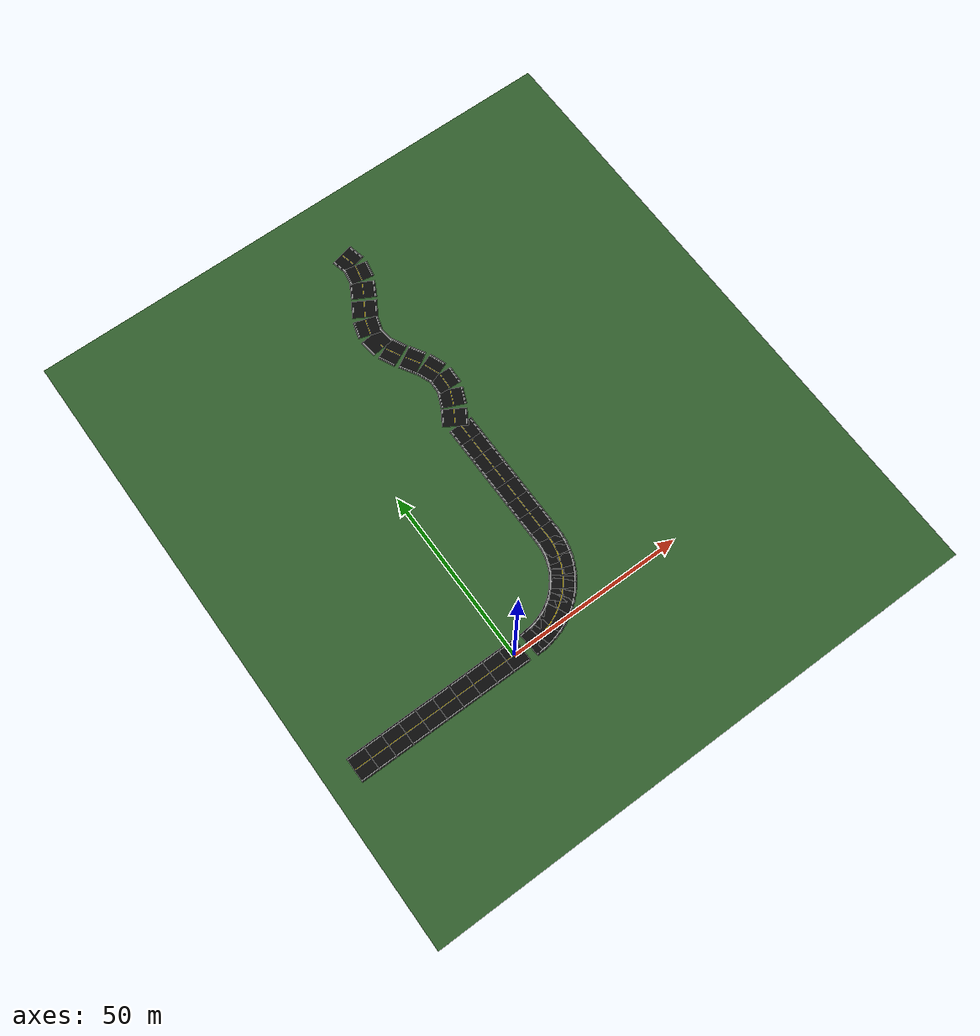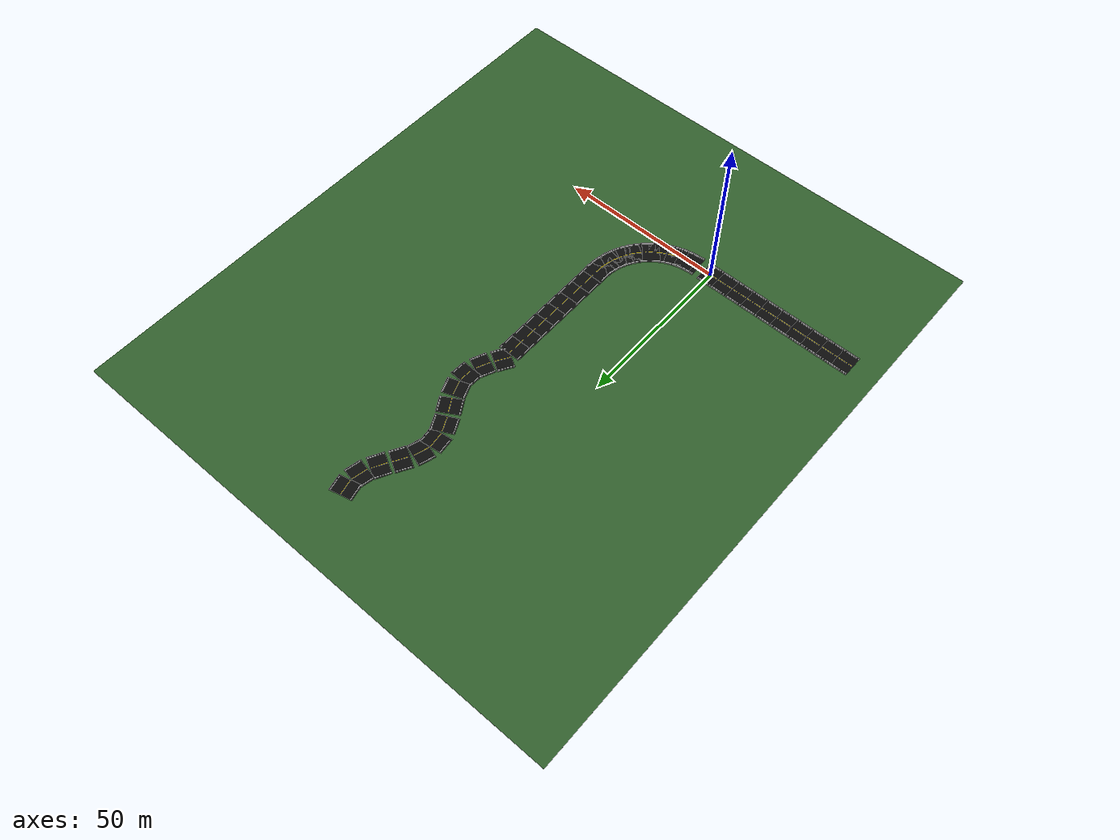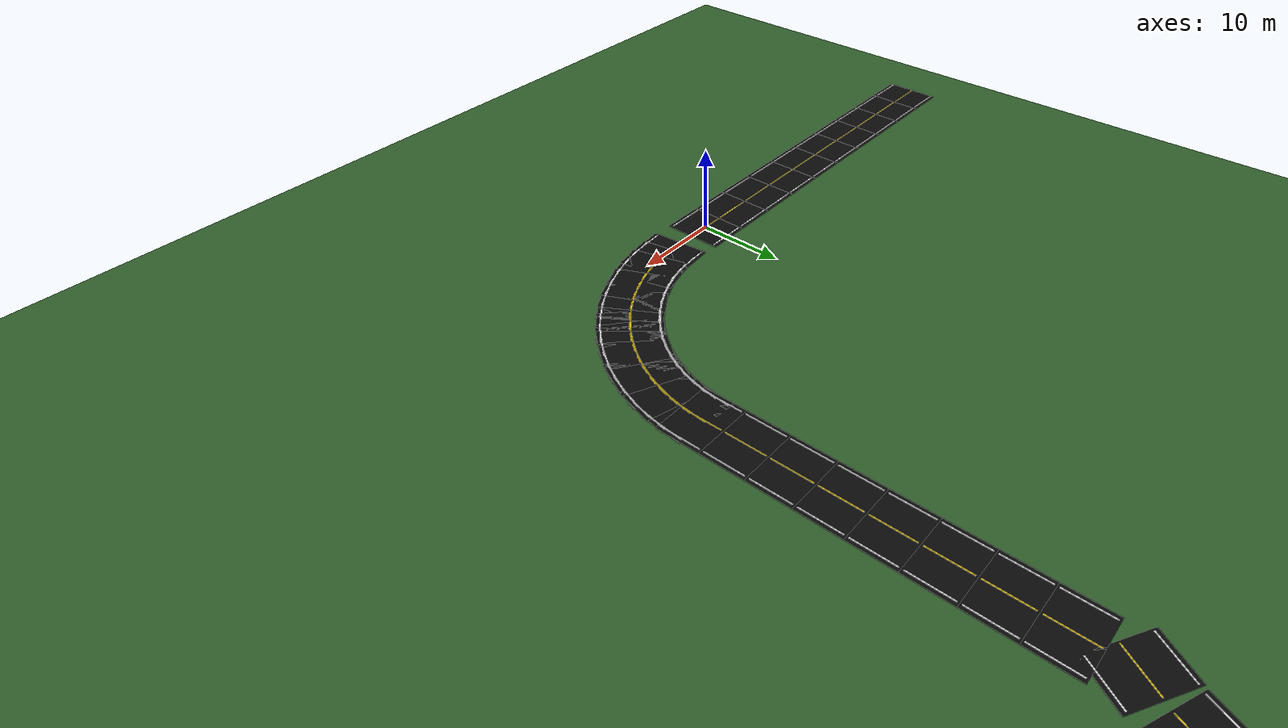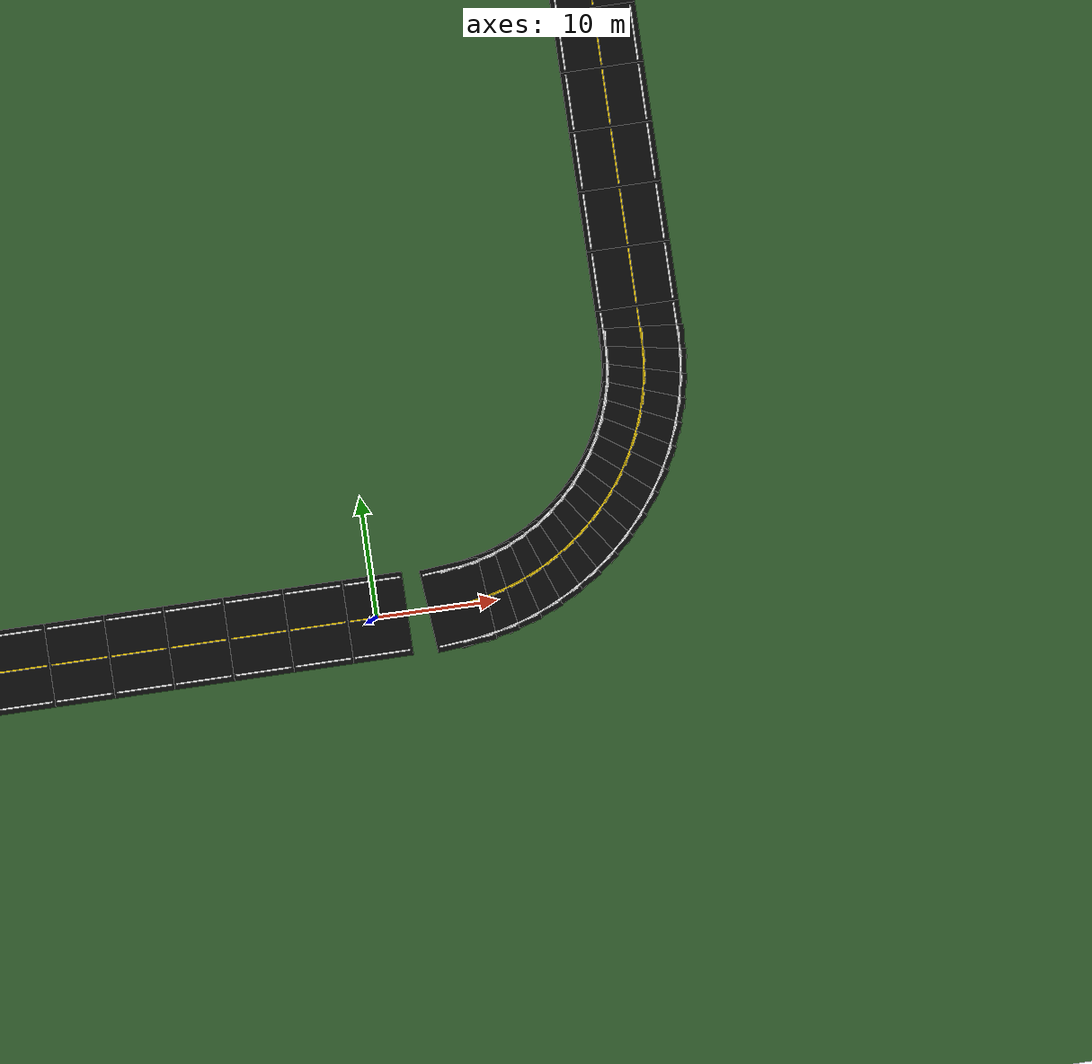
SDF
<?xml version="1.0" ?>
<sdf version="1.6">
  <world name="curved_road_world">

    <physics name="default_physics" type="ode">
      <max_step_size>0.001</max_step_size>
      <real_time_update_rate>1000</real_time_update_rate>
      <real_time_factor>1.0</real_time_factor>
    </physics>

    <scene>
      <ambient>0.45 0.45 0.45 1</ambient>
      <background>0.7 0.8 1.0 1</background>
      <shadows>true</shadows>
    </scene>

    <include>
      <uri>model://sun</uri>
    </include>

    <model name="grass_ground">
      <static>true</static>
      <pose>25 45 -0.02 0 0 0</pose>
      <link name="ground_link">
        <collision name="ground_collision">
          <geometry>
            <box>
              <size>160 180 0.02</size>
            </box>
          </geometry>
        </collision>
        <visual name="ground_visual">
          <geometry>
            <box>
              <size>160 180 0.02</size>
            </box>
          </geometry>
          <material>
            <ambient>0.18 0.35 0.16 1</ambient>
            <diffuse>0.18 0.35 0.16 1</diffuse>
          </material>
        </visual>
      </link>
    </model>

    <model name="road_straight_00">
      <static>true</static>
      <pose>-45.000 0.000 0.015 0 0 0.000000</pose>
      <link name="road_link">
        <collision name="road_collision">
          <geometry>
            <box>
              <size>5.000 7.000 0.04</size>
            </box>
          </geometry>
        </collision>
        <visual name="road_visual">
          <geometry>
            <box>
              <size>5.000 7.000 0.04</size>
            </box>
          </geometry>
          <material>
            <ambient>0.025 0.025 0.025 1</ambient>
            <diffuse>0.035 0.035 0.035 1</diffuse>
            <specular>0.01 0.01 0.01 1</specular>
          </material>
        </visual>
      </link>
    </model>
    <model name="road_straight_01">
      <static>true</static>
      <pose>-40.000 0.000 0.015 0 0 0.000000</pose>
      <link name="road_link">
        <collision name="road_collision">
          <geometry>
            <box>
              <size>5.000 7.000 0.04</size>
            </box>
          </geometry>
        </collision>
        <visual name="road_visual">
          <geometry>
            <box>
              <size>5.000 7.000 0.04</size>
            </box>
          </geometry>
          <material>
            <ambient>0.025 0.025 0.025 1</ambient>
            <diffuse>0.035 0.035 0.035 1</diffuse>
            <specular>0.01 0.01 0.01 1</specular>
          </material>
        </visual>
      </link>
    </model>
    <model name="road_straight_02">
      <static>true</static>
      <pose>-35.000 0.000 0.015 0 0 0.000000</pose>
      <link name="road_link">
        <collision name="road_collision">
          <geometry>
            <box>
              <size>5.000 7.000 0.04</size>
            </box>
          </geometry>
        </collision>
        <visual name="road_visual">
          <geometry>
            <box>
              <size>5.000 7.000 0.04</size>
            </box>
          </geometry>
          <material>
            <ambient>0.025 0.025 0.025 1</ambient>
            <diffuse>0.035 0.035 0.035 1</diffuse>
            <specular>0.01 0.01 0.01 1</specular>
          </material>
        </visual>
      </link>
    </model>
    <model name="road_straight_03">
      <static>true</static>
      <pose>-30.000 0.000 0.015 0 0 0.000000</pose>
      <link name="road_link">
        <collision name="road_collision">
          <geometry>
            <box>
              <size>5.000 7.000 0.04</size>
            </box>
          </geometry>
        </collision>
        <visual name="road_visual">
          <geometry>
            <box>
              <size>5.000 7.000 0.04</size>
            </box>
          </geometry>
          <material>
            <ambient>0.025 0.025 0.025 1</ambient>
            <diffuse>0.035 0.035 0.035 1</diffuse>
            <specular>0.01 0.01 0.01 1</specular>
          </material>
        </visual>
      </link>
    </model>
    <model name="road_straight_04">
      <static>true</static>
      <pose>-25.000 0.000 0.015 0 0 0.000000</pose>
      <link name="road_link">
        <collision name="road_collision">
          <geometry>
            <box>
              <size>5.000 7.000 0.04</size>
            </box>
          </geometry>
        </collision>
        <visual name="road_visual">
          <geometry>
            <box>
              <size>5.000 7.000 0.04</size>
            </box>
          </geometry>
          <material>
            <ambient>0.025 0.025 0.025 1</ambient>
            <diffuse>0.035 0.035 0.035 1</diffuse>
            <specular>0.01 0.01 0.01 1</specular>
          </material>
        </visual>
      </link>
    </model>
    <model name="road_straight_05">
      <static>true</static>
      <pose>-20.000 0.000 0.015 0 0 0.000000</pose>
      <link name="road_link">
        <collision name="road_collision">
          <geometry>
            <box>
              <size>5.000 7.000 0.04</size>
            </box>
          </geometry>
        </collision>
        <visual name="road_visual">
          <geometry>
            <box>
              <size>5.000 7.000 0.04</size>
            </box>
          </geometry>
          <material>
            <ambient>0.025 0.025 0.025 1</ambient>
            <diffuse>0.035 0.035 0.035 1</diffuse>
            <specular>0.01 0.01 0.01 1</specular>
          </material>
        </visual>
      </link>
    </model>
    <model name="road_straight_06">
      <static>true</static>
      <pose>-15.000 0.000 0.015 0 0 0.000000</pose>
      <link name="road_link">
        <collision name="road_collision">
          <geometry>
            <box>
              <size>5.000 7.000 0.04</size>
            </box>
          </geometry>
        </collision>
        <visual name="road_visual">
          <geometry>
            <box>
              <size>5.000 7.000 0.04</size>
            </box>
          </geometry>
          <material>
            <ambient>0.025 0.025 0.025 1</ambient>
            <diffuse>0.035 0.035 0.035 1</diffuse>
            <specular>0.01 0.01 0.01 1</specular>
          </material>
        </visual>
      </link>
    </model>
    <model name="road_straight_07">
      <static>true</static>
      <pose>-10.000 0.000 0.015 0 0 0.000000</pose>
      <link name="road_link">
        <collision name="road_collision">
          <geometry>
            <box>
              <size>5.000 7.000 0.04</size>
            </box>
          </geometry>
        </collision>
        <visual name="road_visual">
          <geometry>
            <box>
              <size>5.000 7.000 0.04</size>
            </box>
          </geometry>
          <material>
            <ambient>0.025 0.025 0.025 1</ambient>
            <diffuse>0.035 0.035 0.035 1</diffuse>
            <specular>0.01 0.01 0.01 1</specular>
          </material>
        </visual>
      </link>
    </model>
    <model name="road_straight_08">
      <static>true</static>
      <pose>-5.000 0.000 0.015 0 0 0.000000</pose>
      <link name="road_link">
        <collision name="road_collision">
          <geometry>
            <box>
              <size>5.000 7.000 0.04</size>
            </box>
          </geometry>
        </collision>
        <visual name="road_visual">
          <geometry>
            <box>
              <size>5.000 7.000 0.04</size>
            </box>
          </geometry>
          <material>
            <ambient>0.025 0.025 0.025 1</ambient>
            <diffuse>0.035 0.035 0.035 1</diffuse>
            <specular>0.01 0.01 0.01 1</specular>
          </material>
        </visual>
      </link>
    </model>
    <model name="road_straight_09">
      <static>true</static>
      <pose>0.000 0.000 0.015 0 0 0.000000</pose>
      <link name="road_link">
        <collision name="road_collision">
          <geometry>
            <box>
              <size>5.000 7.000 0.04</size>
            </box>
          </geometry>
        </collision>
        <visual name="road_visual">
          <geometry>
            <box>
              <size>5.000 7.000 0.04</size>
            </box>
          </geometry>
          <material>
            <ambient>0.025 0.025 0.025 1</ambient>
            <diffuse>0.035 0.035 0.035 1</diffuse>
            <specular>0.01 0.01 0.01 1</specular>
          </material>
        </visual>
      </link>
    </model>
    <model name="road_left_90_curve_01">
      <static>true</static>
      <pose>6.743 0.076 0.015 0 0 0.087266</pose>
      <link name="road_link">
        <collision name="road_collision">
          <geometry>
            <box>
              <size>5.000 7.000 0.04</size>
            </box>
          </geometry>
        </collision>
        <visual name="road_visual">
          <geometry>
            <box>
              <size>5.000 7.000 0.04</size>
            </box>
          </geometry>
          <material>
            <ambient>0.025 0.025 0.025 1</ambient>
            <diffuse>0.035 0.035 0.035 1</diffuse>
            <specular>0.01 0.01 0.01 1</specular>
          </material>
        </visual>
      </link>
    </model>
    <model name="road_left_90_curve_02">
      <static>true</static>
      <pose>8.473 0.304 0.015 0 0 0.174533</pose>
      <link name="road_link">
        <collision name="road_collision">
          <geometry>
            <box>
              <size>5.000 7.000 0.04</size>
            </box>
          </geometry>
        </collision>
        <visual name="road_visual">
          <geometry>
            <box>
              <size>5.000 7.000 0.04</size>
            </box>
          </geometry>
          <material>
            <ambient>0.025 0.025 0.025 1</ambient>
            <diffuse>0.035 0.035 0.035 1</diffuse>
            <specular>0.01 0.01 0.01 1</specular>
          </material>
        </visual>
      </link>
    </model>
    <model name="road_left_90_curve_03">
      <static>true</static>
      <pose>10.176 0.681 0.015 0 0 0.261799</pose>
      <link name="road_link">
        <collision name="road_collision">
          <geometry>
            <box>
              <size>5.000 7.000 0.04</size>
            </box>
          </geometry>
        </collision>
        <visual name="road_visual">
          <geometry>
            <box>
              <size>5.000 7.000 0.04</size>
            </box>
          </geometry>
          <material>
            <ambient>0.025 0.025 0.025 1</ambient>
            <diffuse>0.035 0.035 0.035 1</diffuse>
            <specular>0.01 0.01 0.01 1</specular>
          </material>
        </visual>
      </link>
    </model>
    <model name="road_left_90_curve_04">
      <static>true</static>
      <pose>11.840 1.206 0.015 0 0 0.349066</pose>
      <link name="road_link">
        <collision name="road_collision">
          <geometry>
            <box>
              <size>5.000 7.000 0.04</size>
            </box>
          </geometry>
        </collision>
        <visual name="road_visual">
          <geometry>
            <box>
              <size>5.000 7.000 0.04</size>
            </box>
          </geometry>
          <material>
            <ambient>0.025 0.025 0.025 1</ambient>
            <diffuse>0.035 0.035 0.035 1</diffuse>
            <specular>0.01 0.01 0.01 1</specular>
          </material>
        </visual>
      </link>
    </model>
    <model name="road_left_90_curve_05">
      <static>true</static>
      <pose>13.452 1.874 0.015 0 0 0.436332</pose>
      <link name="road_link">
        <collision name="road_collision">
          <geometry>
            <box>
              <size>5.000 7.000 0.04</size>
            </box>
          </geometry>
        </collision>
        <visual name="road_visual">
          <geometry>
            <box>
              <size>5.000 7.000 0.04</size>
            </box>
          </geometry>
          <material>
            <ambient>0.025 0.025 0.025 1</ambient>
            <diffuse>0.035 0.035 0.035 1</diffuse>
            <specular>0.01 0.01 0.01 1</specular>
          </material>
        </visual>
      </link>
    </model>
    <model name="road_left_90_curve_06">
      <static>true</static>
      <pose>15.000 2.679 0.015 0 0 0.523599</pose>
      <link name="road_link">
        <collision name="road_collision">
          <geometry>
            <box>
              <size>5.000 7.000 0.04</size>
            </box>
          </geometry>
        </collision>
        <visual name="road_visual">
          <geometry>
            <box>
              <size>5.000 7.000 0.04</size>
            </box>
          </geometry>
          <material>
            <ambient>0.025 0.025 0.025 1</ambient>
            <diffuse>0.035 0.035 0.035 1</diffuse>
            <specular>0.01 0.01 0.01 1</specular>
          </material>
        </visual>
      </link>
    </model>
    <model name="road_left_90_curve_07">
      <static>true</static>
      <pose>16.472 3.617 0.015 0 0 0.610865</pose>
      <link name="road_link">
        <collision name="road_collision">
          <geometry>
            <box>
              <size>5.000 7.000 0.04</size>
            </box>
          </geometry>
        </collision>
        <visual name="road_visual">
          <geometry>
            <box>
              <size>5.000 7.000 0.04</size>
            </box>
          </geometry>
          <material>
            <ambient>0.025 0.025 0.025 1</ambient>
            <diffuse>0.035 0.035 0.035 1</diffuse>
            <specular>0.01 0.01 0.01 1</specular>
          </material>
        </visual>
      </link>
    </model>
    <model name="road_left_90_curve_08">
      <static>true</static>
      <pose>17.856 4.679 0.015 0 0 0.698132</pose>
      <link name="road_link">
        <collision name="road_collision">
          <geometry>
            <box>
              <size>5.000 7.000 0.04</size>
            </box>
          </geometry>
        </collision>
        <visual name="road_visual">
          <geometry>
            <box>
              <size>5.000 7.000 0.04</size>
            </box>
          </geometry>
          <material>
            <ambient>0.025 0.025 0.025 1</ambient>
            <diffuse>0.035 0.035 0.035 1</diffuse>
            <specular>0.01 0.01 0.01 1</specular>
          </material>
        </visual>
      </link>
    </model>
    <model name="road_left_90_curve_09">
      <static>true</static>
      <pose>19.142 5.858 0.015 0 0 0.785398</pose>
      <link name="road_link">
        <collision name="road_collision">
          <geometry>
            <box>
              <size>5.000 7.000 0.04</size>
            </box>
          </geometry>
        </collision>
        <visual name="road_visual">
          <geometry>
            <box>
              <size>5.000 7.000 0.04</size>
            </box>
          </geometry>
          <material>
            <ambient>0.025 0.025 0.025 1</ambient>
            <diffuse>0.035 0.035 0.035 1</diffuse>
            <specular>0.01 0.01 0.01 1</specular>
          </material>
        </visual>
      </link>
    </model>
    <model name="road_left_90_curve_10">
      <static>true</static>
      <pose>20.321 7.144 0.015 0 0 0.872665</pose>
      <link name="road_link">
        <collision name="road_collision">
          <geometry>
            <box>
              <size>5.000 7.000 0.04</size>
            </box>
          </geometry>
        </collision>
        <visual name="road_visual">
          <geometry>
            <box>
              <size>5.000 7.000 0.04</size>
            </box>
          </geometry>
          <material>
            <ambient>0.025 0.025 0.025 1</ambient>
            <diffuse>0.035 0.035 0.035 1</diffuse>
            <specular>0.01 0.01 0.01 1</specular>
          </material>
        </visual>
      </link>
    </model>
    <model name="road_left_90_curve_11">
      <static>true</static>
      <pose>21.383 8.528 0.015 0 0 0.959931</pose>
      <link name="road_link">
        <collision name="road_collision">
          <geometry>
            <box>
              <size>5.000 7.000 0.04</size>
            </box>
          </geometry>
        </collision>
        <visual name="road_visual">
          <geometry>
            <box>
              <size>5.000 7.000 0.04</size>
            </box>
          </geometry>
          <material>
            <ambient>0.025 0.025 0.025 1</ambient>
            <diffuse>0.035 0.035 0.035 1</diffuse>
            <specular>0.01 0.01 0.01 1</specular>
          </material>
        </visual>
      </link>
    </model>
    <model name="road_left_90_curve_12">
      <static>true</static>
      <pose>22.321 10.000 0.015 0 0 1.047198</pose>
      <link name="road_link">
        <collision name="road_collision">
          <geometry>
            <box>
              <size>5.000 7.000 0.04</size>
            </box>
          </geometry>
        </collision>
        <visual name="road_visual">
          <geometry>
            <box>
              <size>5.000 7.000 0.04</size>
            </box>
          </geometry>
          <material>
            <ambient>0.025 0.025 0.025 1</ambient>
            <diffuse>0.035 0.035 0.035 1</diffuse>
            <specular>0.01 0.01 0.01 1</specular>
          </material>
        </visual>
      </link>
    </model>
    <model name="road_left_90_curve_13">
      <static>true</static>
      <pose>23.126 11.548 0.015 0 0 1.134464</pose>
      <link name="road_link">
        <collision name="road_collision">
          <geometry>
            <box>
              <size>5.000 7.000 0.04</size>
            </box>
          </geometry>
        </collision>
        <visual name="road_visual">
          <geometry>
            <box>
              <size>5.000 7.000 0.04</size>
            </box>
          </geometry>
          <material>
            <ambient>0.025 0.025 0.025 1</ambient>
            <diffuse>0.035 0.035 0.035 1</diffuse>
            <specular>0.01 0.01 0.01 1</specular>
          </material>
        </visual>
      </link>
    </model>
    <model name="road_left_90_curve_14">
      <static>true</static>
      <pose>23.794 13.160 0.015 0 0 1.221730</pose>
      <link name="road_link">
        <collision name="road_collision">
          <geometry>
            <box>
              <size>5.000 7.000 0.04</size>
            </box>
          </geometry>
        </collision>
        <visual name="road_visual">
          <geometry>
            <box>
              <size>5.000 7.000 0.04</size>
            </box>
          </geometry>
          <material>
            <ambient>0.025 0.025 0.025 1</ambient>
            <diffuse>0.035 0.035 0.035 1</diffuse>
            <specular>0.01 0.01 0.01 1</specular>
          </material>
        </visual>
      </link>
    </model>
    <model name="road_left_90_curve_15">
      <static>true</static>
      <pose>24.319 14.824 0.015 0 0 1.308997</pose>
      <link name="road_link">
        <collision name="road_collision">
          <geometry>
            <box>
              <size>5.000 7.000 0.04</size>
            </box>
          </geometry>
        </collision>
        <visual name="road_visual">
          <geometry>
            <box>
              <size>5.000 7.000 0.04</size>
            </box>
          </geometry>
          <material>
            <ambient>0.025 0.025 0.025 1</ambient>
            <diffuse>0.035 0.035 0.035 1</diffuse>
            <specular>0.01 0.01 0.01 1</specular>
          </material>
        </visual>
      </link>
    </model>
    <model name="road_left_90_curve_16">
      <static>true</static>
      <pose>24.696 16.527 0.015 0 0 1.396263</pose>
      <link name="road_link">
        <collision name="road_collision">
          <geometry>
            <box>
              <size>5.000 7.000 0.04</size>
            </box>
          </geometry>
        </collision>
        <visual name="road_visual">
          <geometry>
            <box>
              <size>5.000 7.000 0.04</size>
            </box>
          </geometry>
          <material>
            <ambient>0.025 0.025 0.025 1</ambient>
            <diffuse>0.035 0.035 0.035 1</diffuse>
            <specular>0.01 0.01 0.01 1</specular>
          </material>
        </visual>
      </link>
    </model>
    <model name="road_left_90_curve_17">
      <static>true</static>
      <pose>24.924 18.257 0.015 0 0 1.483530</pose>
      <link name="road_link">
        <collision name="road_collision">
          <geometry>
            <box>
              <size>5.000 7.000 0.04</size>
            </box>
          </geometry>
        </collision>
        <visual name="road_visual">
          <geometry>
            <box>
              <size>5.000 7.000 0.04</size>
            </box>
          </geometry>
          <material>
            <ambient>0.025 0.025 0.025 1</ambient>
            <diffuse>0.035 0.035 0.035 1</diffuse>
            <specular>0.01 0.01 0.01 1</specular>
          </material>
        </visual>
      </link>
    </model>
    <model name="road_left_90_curve_18">
      <static>true</static>
      <pose>25.000 20.000 0.015 0 0 1.570796</pose>
      <link name="road_link">
        <collision name="road_collision">
          <geometry>
            <box>
              <size>5.000 7.000 0.04</size>
            </box>
          </geometry>
        </collision>
        <visual name="road_visual">
          <geometry>
            <box>
              <size>5.000 7.000 0.04</size>
            </box>
          </geometry>
          <material>
            <ambient>0.025 0.025 0.025 1</ambient>
            <diffuse>0.035 0.035 0.035 1</diffuse>
            <specular>0.01 0.01 0.01 1</specular>
          </material>
        </visual>
      </link>
    </model>
    <model name="road_post_curve_straight_01">
      <static>true</static>
      <pose>25.000 25.000 0.015 0 0 1.570796</pose>
      <link name="road_link">
        <collision name="road_collision">
          <geometry>
            <box>
              <size>5.000 7.000 0.04</size>
            </box>
          </geometry>
        </collision>
        <visual name="road_visual">
          <geometry>
            <box>
              <size>5.000 7.000 0.04</size>
            </box>
          </geometry>
          <material>
            <ambient>0.025 0.025 0.025 1</ambient>
            <diffuse>0.035 0.035 0.035 1</diffuse>
            <specular>0.01 0.01 0.01 1</specular>
          </material>
        </visual>
      </link>
    </model>
    <model name="road_post_curve_straight_02">
      <static>true</static>
      <pose>25.000 30.000 0.015 0 0 1.570796</pose>
      <link name="road_link">
        <collision name="road_collision">
          <geometry>
            <box>
              <size>5.000 7.000 0.04</size>
            </box>
          </geometry>
        </collision>
        <visual name="road_visual">
          <geometry>
            <box>
              <size>5.000 7.000 0.04</size>
            </box>
          </geometry>
          <material>
            <ambient>0.025 0.025 0.025 1</ambient>
            <diffuse>0.035 0.035 0.035 1</diffuse>
            <specular>0.01 0.01 0.01 1</specular>
          </material>
        </visual>
      </link>
    </model>
    <model name="road_post_curve_straight_03">
      <static>true</static>
      <pose>25.000 35.000 0.015 0 0 1.570796</pose>
      <link name="road_link">
        <collision name="road_collision">
          <geometry>
            <box>
              <size>5.000 7.000 0.04</size>
            </box>
          </geometry>
        </collision>
        <visual name="road_visual">
          <geometry>
            <box>
              <size>5.000 7.000 0.04</size>
            </box>
          </geometry>
          <material>
            <ambient>0.025 0.025 0.025 1</ambient>
            <diffuse>0.035 0.035 0.035 1</diffuse>
            <specular>0.01 0.01 0.01 1</specular>
          </material>
        </visual>
      </link>
    </model>
    <model name="road_post_curve_straight_04">
      <static>true</static>
      <pose>25.000 40.000 0.015 0 0 1.570796</pose>
      <link name="road_link">
        <collision name="road_collision">
          <geometry>
            <box>
              <size>5.000 7.000 0.04</size>
            </box>
          </geometry>
        </collision>
        <visual name="road_visual">
          <geometry>
            <box>
              <size>5.000 7.000 0.04</size>
            </box>
          </geometry>
          <material>
            <ambient>0.025 0.025 0.025 1</ambient>
            <diffuse>0.035 0.035 0.035 1</diffuse>
            <specular>0.01 0.01 0.01 1</specular>
          </material>
        </visual>
      </link>
    </model>
    <model name="road_post_curve_straight_05">
      <static>true</static>
      <pose>25.000 45.000 0.015 0 0 1.570796</pose>
      <link name="road_link">
        <collision name="road_collision">
          <geometry>
            <box>
              <size>5.000 7.000 0.04</size>
            </box>
          </geometry>
        </collision>
        <visual name="road_visual">
          <geometry>
            <box>
              <size>5.000 7.000 0.04</size>
            </box>
          </geometry>
          <material>
            <ambient>0.025 0.025 0.025 1</ambient>
            <diffuse>0.035 0.035 0.035 1</diffuse>
            <specular>0.01 0.01 0.01 1</specular>
          </material>
        </visual>
      </link>
    </model>
    <model name="road_post_curve_straight_06">
      <static>true</static>
      <pose>25.000 50.000 0.015 0 0 1.570796</pose>
      <link name="road_link">
        <collision name="road_collision">
          <geometry>
            <box>
              <size>5.000 7.000 0.04</size>
            </box>
          </geometry>
        </collision>
        <visual name="road_visual">
          <geometry>
            <box>
              <size>5.000 7.000 0.04</size>
            </box>
          </geometry>
          <material>
            <ambient>0.025 0.025 0.025 1</ambient>
            <diffuse>0.035 0.035 0.035 1</diffuse>
            <specular>0.01 0.01 0.01 1</specular>
          </material>
        </visual>
      </link>
    </model>
    <model name="road_post_curve_straight_07">
      <static>true</static>
      <pose>25.000 55.000 0.015 0 0 1.570796</pose>
      <link name="road_link">
        <collision name="road_collision">
          <geometry>
            <box>
              <size>5.000 7.000 0.04</size>
            </box>
          </geometry>
        </collision>
        <visual name="road_visual">
          <geometry>
            <box>
              <size>5.000 7.000 0.04</size>
            </box>
          </geometry>
          <material>
            <ambient>0.025 0.025 0.025 1</ambient>
            <diffuse>0.035 0.035 0.035 1</diffuse>
            <specular>0.01 0.01 0.01 1</specular>
          </material>
        </visual>
      </link>
    </model>
    <model name="road_small_s_curve_00">
      <static>true</static>
      <pose>25.000 60.000 0.015 0 0 1.030377</pose>
      <link name="road_link">
        <collision name="road_collision">
          <geometry>
            <box>
              <size>5.000 7.000 0.04</size>
            </box>
          </geometry>
        </collision>
        <visual name="road_visual">
          <geometry>
            <box>
              <size>5.000 7.000 0.04</size>
            </box>
          </geometry>
          <material>
            <ambient>0.025 0.025 0.025 1</ambient>
            <diffuse>0.035 0.035 0.035 1</diffuse>
            <specular>0.01 0.01 0.01 1</specular>
          </material>
        </visual>
      </link>
    </model>
    <model name="road_small_s_curve_01">
      <static>true</static>
      <pose>27.727 65.000 0.015 0 0 1.157116</pose>
      <link name="road_link">
        <collision name="road_collision">
          <geometry>
            <box>
              <size>5.000 7.000 0.04</size>
            </box>
          </geometry>
        </collision>
        <visual name="road_visual">
          <geometry>
            <box>
              <size>5.000 7.000 0.04</size>
            </box>
          </geometry>
          <material>
            <ambient>0.025 0.025 0.025 1</ambient>
            <diffuse>0.035 0.035 0.035 1</diffuse>
            <specular>0.01 0.01 0.01 1</specular>
          </material>
        </visual>
      </link>
    </model>
    <model name="road_small_s_curve_02">
      <static>true</static>
      <pose>28.990 70.000 0.015 0 0 1.528379</pose>
      <link name="road_link">
        <collision name="road_collision">
          <geometry>
            <box>
              <size>5.000 7.000 0.04</size>
            </box>
          </geometry>
        </collision>
        <visual name="road_visual">
          <geometry>
            <box>
              <size>5.000 7.000 0.04</size>
            </box>
          </geometry>
          <material>
            <ambient>0.025 0.025 0.025 1</ambient>
            <diffuse>0.035 0.035 0.035 1</diffuse>
            <specular>0.01 0.01 0.01 1</specular>
          </material>
        </visual>
      </link>
    </model>
    <model name="road_small_s_curve_03">
      <static>true</static>
      <pose>28.112 75.000 0.015 0 0 1.931235</pose>
      <link name="road_link">
        <collision name="road_collision">
          <geometry>
            <box>
              <size>5.000 7.000 0.04</size>
            </box>
          </geometry>
        </collision>
        <visual name="road_visual">
          <geometry>
            <box>
              <size>5.000 7.000 0.04</size>
            </box>
          </geometry>
          <material>
            <ambient>0.025 0.025 0.025 1</ambient>
            <diffuse>0.035 0.035 0.035 1</diffuse>
            <specular>0.01 0.01 0.01 1</specular>
          </material>
        </visual>
      </link>
    </model>
    <model name="road_small_s_curve_04">
      <static>true</static>
      <pose>25.564 80.000 0.015 0 0 2.106789</pose>
      <link name="road_link">
        <collision name="road_collision">
          <geometry>
            <box>
              <size>5.000 7.000 0.04</size>
            </box>
          </geometry>
        </collision>
        <visual name="road_visual">
          <geometry>
            <box>
              <size>5.000 7.000 0.04</size>
            </box>
          </geometry>
          <material>
            <ambient>0.025 0.025 0.025 1</ambient>
            <diffuse>0.035 0.035 0.035 1</diffuse>
            <specular>0.01 0.01 0.01 1</specular>
          </material>
        </visual>
      </link>
    </model>
    <model name="road_small_s_curve_05">
      <static>true</static>
      <pose>22.714 85.000 0.015 0 0 2.028294</pose>
      <link name="road_link">
        <collision name="road_collision">
          <geometry>
            <box>
              <size>5.000 7.000 0.04</size>
            </box>
          </geometry>
        </collision>
        <visual name="road_visual">
          <geometry>
            <box>
              <size>5.000 7.000 0.04</size>
            </box>
          </geometry>
          <material>
            <ambient>0.025 0.025 0.025 1</ambient>
            <diffuse>0.035 0.035 0.035 1</diffuse>
            <specular>0.01 0.01 0.01 1</specular>
          </material>
        </visual>
      </link>
    </model>
    <model name="road_small_s_curve_06">
      <static>true</static>
      <pose>21.090 90.000 0.015 0 0 1.696606</pose>
      <link name="road_link">
        <collision name="road_collision">
          <geometry>
            <box>
              <size>5.000 7.000 0.04</size>
            </box>
          </geometry>
        </collision>
        <visual name="road_visual">
          <geometry>
            <box>
              <size>5.000 7.000 0.04</size>
            </box>
          </geometry>
          <material>
            <ambient>0.025 0.025 0.025 1</ambient>
            <diffuse>0.035 0.035 0.035 1</diffuse>
            <specular>0.01 0.01 0.01 1</specular>
          </material>
        </visual>
      </link>
    </model>
    <model name="road_small_s_curve_07">
      <static>true</static>
      <pose>21.564 95.000 0.015 0 0 1.272700</pose>
      <link name="road_link">
        <collision name="road_collision">
          <geometry>
            <box>
              <size>5.000 7.000 0.04</size>
            </box>
          </geometry>
        </collision>
        <visual name="road_visual">
          <geometry>
            <box>
              <size>5.000 7.000 0.04</size>
            </box>
          </geometry>
          <material>
            <ambient>0.025 0.025 0.025 1</ambient>
            <diffuse>0.035 0.035 0.035 1</diffuse>
            <specular>0.01 0.01 0.01 1</specular>
          </material>
        </visual>
      </link>
    </model>
    <model name="road_small_s_curve_08">
      <static>true</static>
      <pose>23.882 100.000 0.015 0 0 1.048134</pose>
      <link name="road_link">
        <collision name="road_collision">
          <geometry>
            <box>
              <size>5.000 7.000 0.04</size>
            </box>
          </geometry>
        </collision>
        <visual name="road_visual">
          <geometry>
            <box>
              <size>5.000 7.000 0.04</size>
            </box>
          </geometry>
          <material>
            <ambient>0.025 0.025 0.025 1</ambient>
            <diffuse>0.035 0.035 0.035 1</diffuse>
            <specular>0.01 0.01 0.01 1</specular>
          </material>
        </visual>
      </link>
    </model>
    <model name="road_small_s_curve_09">
      <static>true</static>
      <pose>26.800 105.000 0.015 0 0 1.078918</pose>
      <link name="road_link">
        <collision name="road_collision">
          <geometry>
            <box>
              <size>5.000 7.000 0.04</size>
            </box>
          </geometry>
        </collision>
        <visual name="road_visual">
          <geometry>
            <box>
              <size>5.000 7.000 0.04</size>
            </box>
          </geometry>
          <material>
            <ambient>0.025 0.025 0.025 1</ambient>
            <diffuse>0.035 0.035 0.035 1</diffuse>
            <specular>0.01 0.01 0.01 1</specular>
          </material>
        </visual>
      </link>
    </model>
    <model name="road_small_s_curve_10">
      <static>true</static>
      <pose>28.752 110.000 0.015 0 0 1.365738</pose>
      <link name="road_link">
        <collision name="road_collision">
          <geometry>
            <box>
              <size>5.000 7.000 0.04</size>
            </box>
          </geometry>
        </collision>
        <visual name="road_visual">
          <geometry>
            <box>
              <size>5.000 7.000 0.04</size>
            </box>
          </geometry>
          <material>
            <ambient>0.025 0.025 0.025 1</ambient>
            <diffuse>0.035 0.035 0.035 1</diffuse>
            <specular>0.01 0.01 0.01 1</specular>
          </material>
        </visual>
      </link>
    </model>
    <model name="road_small_s_curve_11">
      <static>true</static>
      <pose>28.690 115.000 0.015 0 0 1.798240</pose>
      <link name="road_link">
        <collision name="road_collision">
          <geometry>
            <box>
              <size>5.000 7.000 0.04</size>
            </box>
          </geometry>
        </collision>
        <visual name="road_visual">
          <geometry>
            <box>
              <size>5.000 7.000 0.04</size>
            </box>
          </geometry>
          <material>
            <ambient>0.025 0.025 0.025 1</ambient>
            <diffuse>0.035 0.035 0.035 1</diffuse>
            <specular>0.01 0.01 0.01 1</specular>
          </material>
        </visual>
      </link>
    </model>

    <model name="left_edge_straight_00">
      <static>true</static>
      <pose>-45.000 3.050 0.050 0 0 0.000000</pose>
      <link name="line_link">
        <visual name="line_visual">
          <geometry>
            <box>
              <size>4.600 0.120 0.012</size>
            </box>
          </geometry>

          <material>
            <ambient>1 1 1 1</ambient>
            <diffuse>1 1 1 1</diffuse>
          </material>
        </visual>
      </link>
    </model>
    <model name="right_edge_straight_00">
      <static>true</static>
      <pose>-45.000 -3.050 0.050 0 0 0.000000</pose>
      <link name="line_link">
        <visual name="line_visual">
          <geometry>
            <box>
              <size>4.600 0.120 0.012</size>
            </box>
          </geometry>

          <material>
            <ambient>1 1 1 1</ambient>
            <diffuse>1 1 1 1</diffuse>
          </material>
        </visual>
      </link>
    </model>
    <model name="center_line_straight_00">
      <static>true</static>
      <pose>-45.000 0.000 0.050 0 0 0.000000</pose>
      <link name="line_link">
        <visual name="line_visual">
          <geometry>
            <box>
              <size>4.600 0.120 0.012</size>
            </box>
          </geometry>

          <material>
            <ambient>1 0.85 0.05 1</ambient>
            <diffuse>1 0.85 0.05 1</diffuse>
          </material>
        </visual>
      </link>
    </model>
    <model name="left_edge_straight_01">
      <static>true</static>
      <pose>-40.000 3.050 0.050 0 0 0.000000</pose>
      <link name="line_link">
        <visual name="line_visual">
          <geometry>
            <box>
              <size>4.600 0.120 0.012</size>
            </box>
          </geometry>

          <material>
            <ambient>1 1 1 1</ambient>
            <diffuse>1 1 1 1</diffuse>
          </material>
        </visual>
      </link>
    </model>
    <model name="right_edge_straight_01">
      <static>true</static>
      <pose>-40.000 -3.050 0.050 0 0 0.000000</pose>
      <link name="line_link">
        <visual name="line_visual">
          <geometry>
            <box>
              <size>4.600 0.120 0.012</size>
            </box>
          </geometry>

          <material>
            <ambient>1 1 1 1</ambient>
            <diffuse>1 1 1 1</diffuse>
          </material>
        </visual>
      </link>
    </model>
    <model name="center_line_straight_01">
      <static>true</static>
      <pose>-40.000 0.000 0.050 0 0 0.000000</pose>
      <link name="line_link">
        <visual name="line_visual">
          <geometry>
            <box>
              <size>4.600 0.120 0.012</size>
            </box>
          </geometry>

          <material>
            <ambient>1 0.85 0.05 1</ambient>
            <diffuse>1 0.85 0.05 1</diffuse>
          </material>
        </visual>
      </link>
    </model>
    <model name="left_edge_straight_02">
      <static>true</static>
      <pose>-35.000 3.050 0.050 0 0 0.000000</pose>
      <link name="line_link">
        <visual name="line_visual">
          <geometry>
            <box>
              <size>4.600 0.120 0.012</size>
            </box>
          </geometry>

          <material>
            <ambient>1 1 1 1</ambient>
            <diffuse>1 1 1 1</diffuse>
          </material>
        </visual>
      </link>
    </model>
    <model name="right_edge_straight_02">
      <static>true</static>
      <pose>-35.000 -3.050 0.050 0 0 0.000000</pose>
      <link name="line_link">
        <visual name="line_visual">
          <geometry>
            <box>
              <size>4.600 0.120 0.012</size>
            </box>
          </geometry>

          <material>
            <ambient>1 1 1 1</ambient>
            <diffuse>1 1 1 1</diffuse>
          </material>
        </visual>
      </link>
    </model>
    <model name="center_line_straight_02">
      <static>true</static>
      <pose>-35.000 0.000 0.050 0 0 0.000000</pose>
      <link name="line_link">
        <visual name="line_visual">
          <geometry>
            <box>
              <size>4.600 0.120 0.012</size>
            </box>
          </geometry>

          <material>
            <ambient>1 0.85 0.05 1</ambient>
            <diffuse>1 0.85 0.05 1</diffuse>
          </material>
        </visual>
      </link>
    </model>
    <model name="left_edge_straight_03">
      <static>true</static>
      <pose>-30.000 3.050 0.050 0 0 0.000000</pose>
      <link name="line_link">
        <visual name="line_visual">
          <geometry>
            <box>
              <size>4.600 0.120 0.012</size>
            </box>
          </geometry>

          <material>
            <ambient>1 1 1 1</ambient>
            <diffuse>1 1 1 1</diffuse>
          </material>
        </visual>
      </link>
    </model>
    <model name="right_edge_straight_03">
      <static>true</static>
      <pose>-30.000 -3.050 0.050 0 0 0.000000</pose>
      <link name="line_link">
        <visual name="line_visual">
          <geometry>
            <box>
              <size>4.600 0.120 0.012</size>
            </box>
          </geometry>

          <material>
            <ambient>1 1 1 1</ambient>
            <diffuse>1 1 1 1</diffuse>
          </material>
        </visual>
      </link>
    </model>
    <model name="center_line_straight_03">
      <static>true</static>
      <pose>-30.000 0.000 0.050 0 0 0.000000</pose>
      <link name="line_link">
        <visual name="line_visual">
          <geometry>
            <box>
              <size>4.600 0.120 0.012</size>
            </box>
          </geometry>

          <material>
            <ambient>1 0.85 0.05 1</ambient>
            <diffuse>1 0.85 0.05 1</diffuse>
          </material>
        </visual>
      </link>
    </model>
    <model name="left_edge_straight_04">
      <static>true</static>
      <pose>-25.000 3.050 0.050 0 0 0.000000</pose>
      <link name="line_link">
        <visual name="line_visual">
          <geometry>
            <box>
              <size>4.600 0.120 0.012</size>
            </box>
          </geometry>

          <material>
            <ambient>1 1 1 1</ambient>
            <diffuse>1 1 1 1</diffuse>
          </material>
        </visual>
      </link>
    </model>
    <model name="right_edge_straight_04">
      <static>true</static>
      <pose>-25.000 -3.050 0.050 0 0 0.000000</pose>
      <link name="line_link">
        <visual name="line_visual">
          <geometry>
            <box>
              <size>4.600 0.120 0.012</size>
            </box>
          </geometry>

          <material>
            <ambient>1 1 1 1</ambient>
            <diffuse>1 1 1 1</diffuse>
          </material>
        </visual>
      </link>
    </model>
    <model name="center_line_straight_04">
      <static>true</static>
      <pose>-25.000 0.000 0.050 0 0 0.000000</pose>
      <link name="line_link">
        <visual name="line_visual">
          <geometry>
            <box>
              <size>4.600 0.120 0.012</size>
            </box>
          </geometry>

          <material>
            <ambient>1 0.85 0.05 1</ambient>
            <diffuse>1 0.85 0.05 1</diffuse>
          </material>
        </visual>
      </link>
    </model>
    <model name="left_edge_straight_05">
      <static>true</static>
      <pose>-20.000 3.050 0.050 0 0 0.000000</pose>
      <link name="line_link">
        <visual name="line_visual">
          <geometry>
            <box>
              <size>4.600 0.120 0.012</size>
            </box>
          </geometry>

          <material>
            <ambient>1 1 1 1</ambient>
            <diffuse>1 1 1 1</diffuse>
          </material>
        </visual>
      </link>
    </model>
    <model name="right_edge_straight_05">
      <static>true</static>
      <pose>-20.000 -3.050 0.050 0 0 0.000000</pose>
      <link name="line_link">
        <visual name="line_visual">
          <geometry>
            <box>
              <size>4.600 0.120 0.012</size>
            </box>
          </geometry>

          <material>
            <ambient>1 1 1 1</ambient>
            <diffuse>1 1 1 1</diffuse>
          </material>
        </visual>
      </link>
    </model>
    <model name="center_line_straight_05">
      <static>true</static>
      <pose>-20.000 0.000 0.050 0 0 0.000000</pose>
      <link name="line_link">
        <visual name="line_visual">
          <geometry>
            <box>
              <size>4.600 0.120 0.012</size>
            </box>
          </geometry>

          <material>
            <ambient>1 0.85 0.05 1</ambient>
            <diffuse>1 0.85 0.05 1</diffuse>
          </material>
        </visual>
      </link>
    </model>
    <model name="left_edge_straight_06">
      <static>true</static>
      <pose>-15.000 3.050 0.050 0 0 0.000000</pose>
      <link name="line_link">
        <visual name="line_visual">
          <geometry>
            <box>
              <size>4.600 0.120 0.012</size>
            </box>
          </geometry>

          <material>
            <ambient>1 1 1 1</ambient>
            <diffuse>1 1 1 1</diffuse>
          </material>
        </visual>
      </link>
    </model>
    <model name="right_edge_straight_06">
      <static>true</static>
      <pose>-15.000 -3.050 0.050 0 0 0.000000</pose>
      <link name="line_link">
        <visual name="line_visual">
          <geometry>
            <box>
              <size>4.600 0.120 0.012</size>
            </box>
          </geometry>

          <material>
            <ambient>1 1 1 1</ambient>
            <diffuse>1 1 1 1</diffuse>
          </material>
        </visual>
      </link>
    </model>
    <model name="center_line_straight_06">
      <static>true</static>
      <pose>-15.000 0.000 0.050 0 0 0.000000</pose>
      <link name="line_link">
        <visual name="line_visual">
          <geometry>
            <box>
              <size>4.600 0.120 0.012</size>
            </box>
          </geometry>

          <material>
            <ambient>1 0.85 0.05 1</ambient>
            <diffuse>1 0.85 0.05 1</diffuse>
          </material>
        </visual>
      </link>
    </model>
    <model name="left_edge_straight_07">
      <static>true</static>
      <pose>-10.000 3.050 0.050 0 0 0.000000</pose>
      <link name="line_link">
        <visual name="line_visual">
          <geometry>
            <box>
              <size>4.600 0.120 0.012</size>
            </box>
          </geometry>

          <material>
            <ambient>1 1 1 1</ambient>
            <diffuse>1 1 1 1</diffuse>
          </material>
        </visual>
      </link>
    </model>
    <model name="right_edge_straight_07">
      <static>true</static>
      <pose>-10.000 -3.050 0.050 0 0 0.000000</pose>
      <link name="line_link">
        <visual name="line_visual">
          <geometry>
            <box>
              <size>4.600 0.120 0.012</size>
            </box>
          </geometry>

          <material>
            <ambient>1 1 1 1</ambient>
            <diffuse>1 1 1 1</diffuse>
          </material>
        </visual>
      </link>
    </model>
    <model name="center_line_straight_07">
      <static>true</static>
      <pose>-10.000 0.000 0.050 0 0 0.000000</pose>
      <link name="line_link">
        <visual name="line_visual">
          <geometry>
            <box>
              <size>4.600 0.120 0.012</size>
            </box>
          </geometry>

          <material>
            <ambient>1 0.85 0.05 1</ambient>
            <diffuse>1 0.85 0.05 1</diffuse>
          </material>
        </visual>
      </link>
    </model>
    <model name="left_edge_straight_08">
      <static>true</static>
      <pose>-5.000 3.050 0.050 0 0 0.000000</pose>
      <link name="line_link">
        <visual name="line_visual">
          <geometry>
            <box>
              <size>4.600 0.120 0.012</size>
            </box>
          </geometry>

          <material>
            <ambient>1 1 1 1</ambient>
            <diffuse>1 1 1 1</diffuse>
          </material>
        </visual>
      </link>
    </model>
    <model name="right_edge_straight_08">
      <static>true</static>
      <pose>-5.000 -3.050 0.050 0 0 0.000000</pose>
      <link name="line_link">
        <visual name="line_visual">
          <geometry>
            <box>
              <size>4.600 0.120 0.012</size>
            </box>
          </geometry>

          <material>
            <ambient>1 1 1 1</ambient>
            <diffuse>1 1 1 1</diffuse>
          </material>
        </visual>
      </link>
    </model>
    <model name="center_line_straight_08">
      <static>true</static>
      <pose>-5.000 0.000 0.050 0 0 0.000000</pose>
      <link name="line_link">
        <visual name="line_visual">
          <geometry>
            <box>
              <size>4.600 0.120 0.012</size>
            </box>
          </geometry>

          <material>
            <ambient>1 0.85 0.05 1</ambient>
            <diffuse>1 0.85 0.05 1</diffuse>
          </material>
        </visual>
      </link>
    </model>
    <model name="left_edge_straight_09">
      <static>true</static>
      <pose>0.000 3.050 0.050 0 0 0.000000</pose>
      <link name="line_link">
        <visual name="line_visual">
          <geometry>
            <box>
              <size>4.600 0.120 0.012</size>
            </box>
          </geometry>

          <material>
            <ambient>1 1 1 1</ambient>
            <diffuse>1 1 1 1</diffuse>
          </material>
        </visual>
      </link>
    </model>
    <model name="right_edge_straight_09">
      <static>true</static>
      <pose>0.000 -3.050 0.050 0 0 0.000000</pose>
      <link name="line_link">
        <visual name="line_visual">
          <geometry>
            <box>
              <size>4.600 0.120 0.012</size>
            </box>
          </geometry>

          <material>
            <ambient>1 1 1 1</ambient>
            <diffuse>1 1 1 1</diffuse>
          </material>
        </visual>
      </link>
    </model>
    <model name="center_line_straight_09">
      <static>true</static>
      <pose>0.000 0.000 0.050 0 0 0.000000</pose>
      <link name="line_link">
        <visual name="line_visual">
          <geometry>
            <box>
              <size>4.600 0.120 0.012</size>
            </box>
          </geometry>

          <material>
            <ambient>1 0.85 0.05 1</ambient>
            <diffuse>1 0.85 0.05 1</diffuse>
          </material>
        </visual>
      </link>
    </model>
    <model name="left_edge_left_90_curve_01">
      <static>true</static>
      <pose>6.477 3.114 0.050 0 0 0.087266</pose>
      <link name="line_link">
        <visual name="line_visual">
          <geometry>
            <box>
              <size>4.600 0.120 0.012</size>
            </box>
          </geometry>

          <material>
            <ambient>1 1 1 1</ambient>
            <diffuse>1 1 1 1</diffuse>
          </material>
        </visual>
      </link>
    </model>
    <model name="right_edge_left_90_curve_01">
      <static>true</static>
      <pose>7.009 -2.962 0.050 0 0 0.087266</pose>
      <link name="line_link">
        <visual name="line_visual">
          <geometry>
            <box>
              <size>4.600 0.120 0.012</size>
            </box>
          </geometry>

          <material>
            <ambient>1 1 1 1</ambient>
            <diffuse>1 1 1 1</diffuse>
          </material>
        </visual>
      </link>
    </model>
    <model name="center_line_left_90_curve_01">
      <static>true</static>
      <pose>6.743 0.076 0.050 0 0 0.087266</pose>
      <link name="line_link">
        <visual name="line_visual">
          <geometry>
            <box>
              <size>4.600 0.120 0.012</size>
            </box>
          </geometry>

          <material>
            <ambient>1 0.85 0.05 1</ambient>
            <diffuse>1 0.85 0.05 1</diffuse>
          </material>
        </visual>
      </link>
    </model>
    <model name="left_edge_left_90_curve_02">
      <static>true</static>
      <pose>7.943 3.308 0.050 0 0 0.174533</pose>
      <link name="line_link">
        <visual name="line_visual">
          <geometry>
            <box>
              <size>4.600 0.120 0.012</size>
            </box>
          </geometry>

          <material>
            <ambient>1 1 1 1</ambient>
            <diffuse>1 1 1 1</diffuse>
          </material>
        </visual>
      </link>
    </model>
    <model name="right_edge_left_90_curve_02">
      <static>true</static>
      <pose>9.003 -2.700 0.050 0 0 0.174533</pose>
      <link name="line_link">
        <visual name="line_visual">
          <geometry>
            <box>
              <size>4.600 0.120 0.012</size>
            </box>
          </geometry>

          <material>
            <ambient>1 1 1 1</ambient>
            <diffuse>1 1 1 1</diffuse>
          </material>
        </visual>
      </link>
    </model>
    <model name="center_line_left_90_curve_02">
      <static>true</static>
      <pose>8.473 0.304 0.050 0 0 0.174533</pose>
      <link name="line_link">
        <visual name="line_visual">
          <geometry>
            <box>
              <size>4.600 0.120 0.012</size>
            </box>
          </geometry>

          <material>
            <ambient>1 0.85 0.05 1</ambient>
            <diffuse>1 0.85 0.05 1</diffuse>
          </material>
        </visual>
      </link>
    </model>
    <model name="left_edge_left_90_curve_03">
      <static>true</static>
      <pose>9.387 3.628 0.050 0 0 0.261799</pose>
      <link name="line_link">
        <visual name="line_visual">
          <geometry>
            <box>
              <size>4.600 0.120 0.012</size>
            </box>
          </geometry>

          <material>
            <ambient>1 1 1 1</ambient>
            <diffuse>1 1 1 1</diffuse>
          </material>
        </visual>
      </link>
    </model>
    <model name="right_edge_left_90_curve_03">
      <static>true</static>
      <pose>10.966 -2.265 0.050 0 0 0.261799</pose>
      <link name="line_link">
        <visual name="line_visual">
          <geometry>
            <box>
              <size>4.600 0.120 0.012</size>
            </box>
          </geometry>

          <material>
            <ambient>1 1 1 1</ambient>
            <diffuse>1 1 1 1</diffuse>
          </material>
        </visual>
      </link>
    </model>
    <model name="center_line_left_90_curve_03">
      <static>true</static>
      <pose>10.176 0.681 0.050 0 0 0.261799</pose>
      <link name="line_link">
        <visual name="line_visual">
          <geometry>
            <box>
              <size>4.600 0.120 0.012</size>
            </box>
          </geometry>

          <material>
            <ambient>1 0.85 0.05 1</ambient>
            <diffuse>1 0.85 0.05 1</diffuse>
          </material>
        </visual>
      </link>
    </model>
    <model name="left_edge_left_90_curve_04">
      <static>true</static>
      <pose>10.797 4.072 0.050 0 0 0.349066</pose>
      <link name="line_link">
        <visual name="line_visual">
          <geometry>
            <box>
              <size>4.600 0.120 0.012</size>
            </box>
          </geometry>

          <material>
            <ambient>1 1 1 1</ambient>
            <diffuse>1 1 1 1</diffuse>
          </material>
        </visual>
      </link>
    </model>
    <model name="right_edge_left_90_curve_04">
      <static>true</static>
      <pose>12.884 -1.660 0.050 0 0 0.349066</pose>
      <link name="line_link">
        <visual name="line_visual">
          <geometry>
            <box>
              <size>4.600 0.120 0.012</size>
            </box>
          </geometry>

          <material>
            <ambient>1 1 1 1</ambient>
            <diffuse>1 1 1 1</diffuse>
          </material>
        </visual>
      </link>
    </model>
    <model name="center_line_left_90_curve_04">
      <static>true</static>
      <pose>11.840 1.206 0.050 0 0 0.349066</pose>
      <link name="line_link">
        <visual name="line_visual">
          <geometry>
            <box>
              <size>4.600 0.120 0.012</size>
            </box>
          </geometry>

          <material>
            <ambient>1 0.85 0.05 1</ambient>
            <diffuse>1 0.85 0.05 1</diffuse>
          </material>
        </visual>
      </link>
    </model>
    <model name="left_edge_left_90_curve_05">
      <static>true</static>
      <pose>12.163 4.638 0.050 0 0 0.436332</pose>
      <link name="line_link">
        <visual name="line_visual">
          <geometry>
            <box>
              <size>4.600 0.120 0.012</size>
            </box>
          </geometry>

          <material>
            <ambient>1 1 1 1</ambient>
            <diffuse>1 1 1 1</diffuse>
          </material>
        </visual>
      </link>
    </model>
    <model name="right_edge_left_90_curve_05">
      <static>true</static>
      <pose>14.741 -0.890 0.050 0 0 0.436332</pose>
      <link name="line_link">
        <visual name="line_visual">
          <geometry>
            <box>
              <size>4.600 0.120 0.012</size>
            </box>
          </geometry>

          <material>
            <ambient>1 1 1 1</ambient>
            <diffuse>1 1 1 1</diffuse>
          </material>
        </visual>
      </link>
    </model>
    <model name="center_line_left_90_curve_05">
      <static>true</static>
      <pose>13.452 1.874 0.050 0 0 0.436332</pose>
      <link name="line_link">
        <visual name="line_visual">
          <geometry>
            <box>
              <size>4.600 0.120 0.012</size>
            </box>
          </geometry>

          <material>
            <ambient>1 0.85 0.05 1</ambient>
            <diffuse>1 0.85 0.05 1</diffuse>
          </material>
        </visual>
      </link>
    </model>
    <model name="left_edge_left_90_curve_06">
      <static>true</static>
      <pose>13.475 5.321 0.050 0 0 0.523599</pose>
      <link name="line_link">
        <visual name="line_visual">
          <geometry>
            <box>
              <size>4.600 0.120 0.012</size>
            </box>
          </geometry>

          <material>
            <ambient>1 1 1 1</ambient>
            <diffuse>1 1 1 1</diffuse>
          </material>
        </visual>
      </link>
    </model>
    <model name="right_edge_left_90_curve_06">
      <static>true</static>
      <pose>16.525 0.038 0.050 0 0 0.523599</pose>
      <link name="line_link">
        <visual name="line_visual">
          <geometry>
            <box>
              <size>4.600 0.120 0.012</size>
            </box>
          </geometry>

          <material>
            <ambient>1 1 1 1</ambient>
            <diffuse>1 1 1 1</diffuse>
          </material>
        </visual>
      </link>
    </model>
    <model name="center_line_left_90_curve_06">
      <static>true</static>
      <pose>15.000 2.679 0.050 0 0 0.523599</pose>
      <link name="line_link">
        <visual name="line_visual">
          <geometry>
            <box>
              <size>4.600 0.120 0.012</size>
            </box>
          </geometry>

          <material>
            <ambient>1 0.85 0.05 1</ambient>
            <diffuse>1 0.85 0.05 1</diffuse>
          </material>
        </visual>
      </link>
    </model>
    <model name="left_edge_left_90_curve_07">
      <static>true</static>
      <pose>14.722 6.115 0.050 0 0 0.610865</pose>
      <link name="line_link">
        <visual name="line_visual">
          <geometry>
            <box>
              <size>4.600 0.120 0.012</size>
            </box>
          </geometry>

          <material>
            <ambient>1 1 1 1</ambient>
            <diffuse>1 1 1 1</diffuse>
          </material>
        </visual>
      </link>
    </model>
    <model name="right_edge_left_90_curve_07">
      <static>true</static>
      <pose>18.221 1.119 0.050 0 0 0.610865</pose>
      <link name="line_link">
        <visual name="line_visual">
          <geometry>
            <box>
              <size>4.600 0.120 0.012</size>
            </box>
          </geometry>

          <material>
            <ambient>1 1 1 1</ambient>
            <diffuse>1 1 1 1</diffuse>
          </material>
        </visual>
      </link>
    </model>
    <model name="center_line_left_90_curve_07">
      <static>true</static>
      <pose>16.472 3.617 0.050 0 0 0.610865</pose>
      <link name="line_link">
        <visual name="line_visual">
          <geometry>
            <box>
              <size>4.600 0.120 0.012</size>
            </box>
          </geometry>

          <material>
            <ambient>1 0.85 0.05 1</ambient>
            <diffuse>1 0.85 0.05 1</diffuse>
          </material>
        </visual>
      </link>
    </model>
    <model name="left_edge_left_90_curve_08">
      <static>true</static>
      <pose>15.895 7.016 0.050 0 0 0.698132</pose>
      <link name="line_link">
        <visual name="line_visual">
          <geometry>
            <box>
              <size>4.600 0.120 0.012</size>
            </box>
          </geometry>

          <material>
            <ambient>1 1 1 1</ambient>
            <diffuse>1 1 1 1</diffuse>
          </material>
        </visual>
      </link>
    </model>
    <model name="right_edge_left_90_curve_08">
      <static>true</static>
      <pose>19.816 2.343 0.050 0 0 0.698132</pose>
      <link name="line_link">
        <visual name="line_visual">
          <geometry>
            <box>
              <size>4.600 0.120 0.012</size>
            </box>
          </geometry>

          <material>
            <ambient>1 1 1 1</ambient>
            <diffuse>1 1 1 1</diffuse>
          </material>
        </visual>
      </link>
    </model>
    <model name="center_line_left_90_curve_08">
      <static>true</static>
      <pose>17.856 4.679 0.050 0 0 0.698132</pose>
      <link name="line_link">
        <visual name="line_visual">
          <geometry>
            <box>
              <size>4.600 0.120 0.012</size>
            </box>
          </geometry>

          <material>
            <ambient>1 0.85 0.05 1</ambient>
            <diffuse>1 0.85 0.05 1</diffuse>
          </material>
        </visual>
      </link>
    </model>
    <model name="left_edge_left_90_curve_09">
      <static>true</static>
      <pose>16.985 8.015 0.050 0 0 0.785398</pose>
      <link name="line_link">
        <visual name="line_visual">
          <geometry>
            <box>
              <size>4.600 0.120 0.012</size>
            </box>
          </geometry>

          <material>
            <ambient>1 1 1 1</ambient>
            <diffuse>1 1 1 1</diffuse>
          </material>
        </visual>
      </link>
    </model>
    <model name="right_edge_left_90_curve_09">
      <static>true</static>
      <pose>21.299 3.701 0.050 0 0 0.785398</pose>
      <link name="line_link">
        <visual name="line_visual">
          <geometry>
            <box>
              <size>4.600 0.120 0.012</size>
            </box>
          </geometry>

          <material>
            <ambient>1 1 1 1</ambient>
            <diffuse>1 1 1 1</diffuse>
          </material>
        </visual>
      </link>
    </model>
    <model name="center_line_left_90_curve_09">
      <static>true</static>
      <pose>19.142 5.858 0.050 0 0 0.785398</pose>
      <link name="line_link">
        <visual name="line_visual">
          <geometry>
            <box>
              <size>4.600 0.120 0.012</size>
            </box>
          </geometry>

          <material>
            <ambient>1 0.85 0.05 1</ambient>
            <diffuse>1 0.85 0.05 1</diffuse>
          </material>
        </visual>
      </link>
    </model>
    <model name="left_edge_left_90_curve_10">
      <static>true</static>
      <pose>17.984 9.105 0.050 0 0 0.872665</pose>
      <link name="line_link">
        <visual name="line_visual">
          <geometry>
            <box>
              <size>4.600 0.120 0.012</size>
            </box>
          </geometry>

          <material>
            <ambient>1 1 1 1</ambient>
            <diffuse>1 1 1 1</diffuse>
          </material>
        </visual>
      </link>
    </model>
    <model name="right_edge_left_90_curve_10">
      <static>true</static>
      <pose>22.657 5.184 0.050 0 0 0.872665</pose>
      <link name="line_link">
        <visual name="line_visual">
          <geometry>
            <box>
              <size>4.600 0.120 0.012</size>
            </box>
          </geometry>

          <material>
            <ambient>1 1 1 1</ambient>
            <diffuse>1 1 1 1</diffuse>
          </material>
        </visual>
      </link>
    </model>
    <model name="center_line_left_90_curve_10">
      <static>true</static>
      <pose>20.321 7.144 0.050 0 0 0.872665</pose>
      <link name="line_link">
        <visual name="line_visual">
          <geometry>
            <box>
              <size>4.600 0.120 0.012</size>
            </box>
          </geometry>

          <material>
            <ambient>1 0.85 0.05 1</ambient>
            <diffuse>1 0.85 0.05 1</diffuse>
          </material>
        </visual>
      </link>
    </model>
    <model name="left_edge_left_90_curve_11">
      <static>true</static>
      <pose>18.885 10.278 0.050 0 0 0.959931</pose>
      <link name="line_link">
        <visual name="line_visual">
          <geometry>
            <box>
              <size>4.600 0.120 0.012</size>
            </box>
          </geometry>

          <material>
            <ambient>1 1 1 1</ambient>
            <diffuse>1 1 1 1</diffuse>
          </material>
        </visual>
      </link>
    </model>
    <model name="right_edge_left_90_curve_11">
      <static>true</static>
      <pose>23.881 6.779 0.050 0 0 0.959931</pose>
      <link name="line_link">
        <visual name="line_visual">
          <geometry>
            <box>
              <size>4.600 0.120 0.012</size>
            </box>
          </geometry>

          <material>
            <ambient>1 1 1 1</ambient>
            <diffuse>1 1 1 1</diffuse>
          </material>
        </visual>
      </link>
    </model>
    <model name="center_line_left_90_curve_11">
      <static>true</static>
      <pose>21.383 8.528 0.050 0 0 0.959931</pose>
      <link name="line_link">
        <visual name="line_visual">
          <geometry>
            <box>
              <size>4.600 0.120 0.012</size>
            </box>
          </geometry>

          <material>
            <ambient>1 0.85 0.05 1</ambient>
            <diffuse>1 0.85 0.05 1</diffuse>
          </material>
        </visual>
      </link>
    </model>
    <model name="left_edge_left_90_curve_12">
      <static>true</static>
      <pose>19.679 11.525 0.050 0 0 1.047198</pose>
      <link name="line_link">
        <visual name="line_visual">
          <geometry>
            <box>
              <size>4.600 0.120 0.012</size>
            </box>
          </geometry>

          <material>
            <ambient>1 1 1 1</ambient>
            <diffuse>1 1 1 1</diffuse>
          </material>
        </visual>
      </link>
    </model>
    <model name="right_edge_left_90_curve_12">
      <static>true</static>
      <pose>24.962 8.475 0.050 0 0 1.047198</pose>
      <link name="line_link">
        <visual name="line_visual">
          <geometry>
            <box>
              <size>4.600 0.120 0.012</size>
            </box>
          </geometry>

          <material>
            <ambient>1 1 1 1</ambient>
            <diffuse>1 1 1 1</diffuse>
          </material>
        </visual>
      </link>
    </model>
    <model name="center_line_left_90_curve_12">
      <static>true</static>
      <pose>22.321 10.000 0.050 0 0 1.047198</pose>
      <link name="line_link">
        <visual name="line_visual">
          <geometry>
            <box>
              <size>4.600 0.120 0.012</size>
            </box>
          </geometry>

          <material>
            <ambient>1 0.85 0.05 1</ambient>
            <diffuse>1 0.85 0.05 1</diffuse>
          </material>
        </visual>
      </link>
    </model>
    <model name="left_edge_left_90_curve_13">
      <static>true</static>
      <pose>20.362 12.837 0.050 0 0 1.134464</pose>
      <link name="line_link">
        <visual name="line_visual">
          <geometry>
            <box>
              <size>4.600 0.120 0.012</size>
            </box>
          </geometry>

          <material>
            <ambient>1 1 1 1</ambient>
            <diffuse>1 1 1 1</diffuse>
          </material>
        </visual>
      </link>
    </model>
    <model name="right_edge_left_90_curve_13">
      <static>true</static>
      <pose>25.890 10.259 0.050 0 0 1.134464</pose>
      <link name="line_link">
        <visual name="line_visual">
          <geometry>
            <box>
              <size>4.600 0.120 0.012</size>
            </box>
          </geometry>

          <material>
            <ambient>1 1 1 1</ambient>
            <diffuse>1 1 1 1</diffuse>
          </material>
        </visual>
      </link>
    </model>
    <model name="center_line_left_90_curve_13">
      <static>true</static>
      <pose>23.126 11.548 0.050 0 0 1.134464</pose>
      <link name="line_link">
        <visual name="line_visual">
          <geometry>
            <box>
              <size>4.600 0.120 0.012</size>
            </box>
          </geometry>

          <material>
            <ambient>1 0.85 0.05 1</ambient>
            <diffuse>1 0.85 0.05 1</diffuse>
          </material>
        </visual>
      </link>
    </model>
    <model name="left_edge_left_90_curve_14">
      <static>true</static>
      <pose>20.928 14.203 0.050 0 0 1.221730</pose>
      <link name="line_link">
        <visual name="line_visual">
          <geometry>
            <box>
              <size>4.600 0.120 0.012</size>
            </box>
          </geometry>

          <material>
            <ambient>1 1 1 1</ambient>
            <diffuse>1 1 1 1</diffuse>
          </material>
        </visual>
      </link>
    </model>
    <model name="right_edge_left_90_curve_14">
      <static>true</static>
      <pose>26.660 12.116 0.050 0 0 1.221730</pose>
      <link name="line_link">
        <visual name="line_visual">
          <geometry>
            <box>
              <size>4.600 0.120 0.012</size>
            </box>
          </geometry>

          <material>
            <ambient>1 1 1 1</ambient>
            <diffuse>1 1 1 1</diffuse>
          </material>
        </visual>
      </link>
    </model>
    <model name="center_line_left_90_curve_14">
      <static>true</static>
      <pose>23.794 13.160 0.050 0 0 1.221730</pose>
      <link name="line_link">
        <visual name="line_visual">
          <geometry>
            <box>
              <size>4.600 0.120 0.012</size>
            </box>
          </geometry>

          <material>
            <ambient>1 0.85 0.05 1</ambient>
            <diffuse>1 0.85 0.05 1</diffuse>
          </material>
        </visual>
      </link>
    </model>
    <model name="left_edge_left_90_curve_15">
      <static>true</static>
      <pose>21.372 15.613 0.050 0 0 1.308997</pose>
      <link name="line_link">
        <visual name="line_visual">
          <geometry>
            <box>
              <size>4.600 0.120 0.012</size>
            </box>
          </geometry>

          <material>
            <ambient>1 1 1 1</ambient>
            <diffuse>1 1 1 1</diffuse>
          </material>
        </visual>
      </link>
    </model>
    <model name="right_edge_left_90_curve_15">
      <static>true</static>
      <pose>27.265 14.034 0.050 0 0 1.308997</pose>
      <link name="line_link">
        <visual name="line_visual">
          <geometry>
            <box>
              <size>4.600 0.120 0.012</size>
            </box>
          </geometry>

          <material>
            <ambient>1 1 1 1</ambient>
            <diffuse>1 1 1 1</diffuse>
          </material>
        </visual>
      </link>
    </model>
    <model name="center_line_left_90_curve_15">
      <static>true</static>
      <pose>24.319 14.824 0.050 0 0 1.308997</pose>
      <link name="line_link">
        <visual name="line_visual">
          <geometry>
            <box>
              <size>4.600 0.120 0.012</size>
            </box>
          </geometry>

          <material>
            <ambient>1 0.85 0.05 1</ambient>
            <diffuse>1 0.85 0.05 1</diffuse>
          </material>
        </visual>
      </link>
    </model>
    <model name="left_edge_left_90_curve_16">
      <static>true</static>
      <pose>21.692 17.057 0.050 0 0 1.396263</pose>
      <link name="line_link">
        <visual name="line_visual">
          <geometry>
            <box>
              <size>4.600 0.120 0.012</size>
            </box>
          </geometry>

          <material>
            <ambient>1 1 1 1</ambient>
            <diffuse>1 1 1 1</diffuse>
          </material>
        </visual>
      </link>
    </model>
    <model name="right_edge_left_90_curve_16">
      <static>true</static>
      <pose>27.700 15.997 0.050 0 0 1.396263</pose>
      <link name="line_link">
        <visual name="line_visual">
          <geometry>
            <box>
              <size>4.600 0.120 0.012</size>
            </box>
          </geometry>

          <material>
            <ambient>1 1 1 1</ambient>
            <diffuse>1 1 1 1</diffuse>
          </material>
        </visual>
      </link>
    </model>
    <model name="center_line_left_90_curve_16">
      <static>true</static>
      <pose>24.696 16.527 0.050 0 0 1.396263</pose>
      <link name="line_link">
        <visual name="line_visual">
          <geometry>
            <box>
              <size>4.600 0.120 0.012</size>
            </box>
          </geometry>

          <material>
            <ambient>1 0.85 0.05 1</ambient>
            <diffuse>1 0.85 0.05 1</diffuse>
          </material>
        </visual>
      </link>
    </model>
    <model name="left_edge_left_90_curve_17">
      <static>true</static>
      <pose>21.886 18.523 0.050 0 0 1.483530</pose>
      <link name="line_link">
        <visual name="line_visual">
          <geometry>
            <box>
              <size>4.600 0.120 0.012</size>
            </box>
          </geometry>

          <material>
            <ambient>1 1 1 1</ambient>
            <diffuse>1 1 1 1</diffuse>
          </material>
        </visual>
      </link>
    </model>
    <model name="right_edge_left_90_curve_17">
      <static>true</static>
      <pose>27.962 17.991 0.050 0 0 1.483530</pose>
      <link name="line_link">
        <visual name="line_visual">
          <geometry>
            <box>
              <size>4.600 0.120 0.012</size>
            </box>
          </geometry>

          <material>
            <ambient>1 1 1 1</ambient>
            <diffuse>1 1 1 1</diffuse>
          </material>
        </visual>
      </link>
    </model>
    <model name="center_line_left_90_curve_17">
      <static>true</static>
      <pose>24.924 18.257 0.050 0 0 1.483530</pose>
      <link name="line_link">
        <visual name="line_visual">
          <geometry>
            <box>
              <size>4.600 0.120 0.012</size>
            </box>
          </geometry>

          <material>
            <ambient>1 0.85 0.05 1</ambient>
            <diffuse>1 0.85 0.05 1</diffuse>
          </material>
        </visual>
      </link>
    </model>
    <model name="left_edge_left_90_curve_18">
      <static>true</static>
      <pose>21.950 20.000 0.050 0 0 1.570796</pose>
      <link name="line_link">
        <visual name="line_visual">
          <geometry>
            <box>
              <size>4.600 0.120 0.012</size>
            </box>
          </geometry>

          <material>
            <ambient>1 1 1 1</ambient>
            <diffuse>1 1 1 1</diffuse>
          </material>
        </visual>
      </link>
    </model>
    <model name="right_edge_left_90_curve_18">
      <static>true</static>
      <pose>28.050 20.000 0.050 0 0 1.570796</pose>
      <link name="line_link">
        <visual name="line_visual">
          <geometry>
            <box>
              <size>4.600 0.120 0.012</size>
            </box>
          </geometry>

          <material>
            <ambient>1 1 1 1</ambient>
            <diffuse>1 1 1 1</diffuse>
          </material>
        </visual>
      </link>
    </model>
    <model name="center_line_left_90_curve_18">
      <static>true</static>
      <pose>25.000 20.000 0.050 0 0 1.570796</pose>
      <link name="line_link">
        <visual name="line_visual">
          <geometry>
            <box>
              <size>4.600 0.120 0.012</size>
            </box>
          </geometry>

          <material>
            <ambient>1 0.85 0.05 1</ambient>
            <diffuse>1 0.85 0.05 1</diffuse>
          </material>
        </visual>
      </link>
    </model>
    <model name="left_edge_post_curve_straight_01">
      <static>true</static>
      <pose>21.950 25.000 0.050 0 0 1.570796</pose>
      <link name="line_link">
        <visual name="line_visual">
          <geometry>
            <box>
              <size>4.600 0.120 0.012</size>
            </box>
          </geometry>

          <material>
            <ambient>1 1 1 1</ambient>
            <diffuse>1 1 1 1</diffuse>
          </material>
        </visual>
      </link>
    </model>
    <model name="right_edge_post_curve_straight_01">
      <static>true</static>
      <pose>28.050 25.000 0.050 0 0 1.570796</pose>
      <link name="line_link">
        <visual name="line_visual">
          <geometry>
            <box>
              <size>4.600 0.120 0.012</size>
            </box>
          </geometry>

          <material>
            <ambient>1 1 1 1</ambient>
            <diffuse>1 1 1 1</diffuse>
          </material>
        </visual>
      </link>
    </model>
    <model name="center_line_post_curve_straight_01">
      <static>true</static>
      <pose>25.000 25.000 0.050 0 0 1.570796</pose>
      <link name="line_link">
        <visual name="line_visual">
          <geometry>
            <box>
              <size>4.600 0.120 0.012</size>
            </box>
          </geometry>

          <material>
            <ambient>1 0.85 0.05 1</ambient>
            <diffuse>1 0.85 0.05 1</diffuse>
          </material>
        </visual>
      </link>
    </model>
    <model name="left_edge_post_curve_straight_02">
      <static>true</static>
      <pose>21.950 30.000 0.050 0 0 1.570796</pose>
      <link name="line_link">
        <visual name="line_visual">
          <geometry>
            <box>
              <size>4.600 0.120 0.012</size>
            </box>
          </geometry>

          <material>
            <ambient>1 1 1 1</ambient>
            <diffuse>1 1 1 1</diffuse>
          </material>
        </visual>
      </link>
    </model>
    <model name="right_edge_post_curve_straight_02">
      <static>true</static>
      <pose>28.050 30.000 0.050 0 0 1.570796</pose>
      <link name="line_link">
        <visual name="line_visual">
          <geometry>
            <box>
              <size>4.600 0.120 0.012</size>
            </box>
          </geometry>

          <material>
            <ambient>1 1 1 1</ambient>
            <diffuse>1 1 1 1</diffuse>
          </material>
        </visual>
      </link>
    </model>
    <model name="center_line_post_curve_straight_02">
      <static>true</static>
      <pose>25.000 30.000 0.050 0 0 1.570796</pose>
      <link name="line_link">
        <visual name="line_visual">
          <geometry>
            <box>
              <size>4.600 0.120 0.012</size>
            </box>
          </geometry>

          <material>
            <ambient>1 0.85 0.05 1</ambient>
            <diffuse>1 0.85 0.05 1</diffuse>
          </material>
        </visual>
      </link>
    </model>
    <model name="left_edge_post_curve_straight_03">
      <static>true</static>
      <pose>21.950 35.000 0.050 0 0 1.570796</pose>
      <link name="line_link">
        <visual name="line_visual">
          <geometry>
            <box>
              <size>4.600 0.120 0.012</size>
            </box>
          </geometry>

          <material>
            <ambient>1 1 1 1</ambient>
            <diffuse>1 1 1 1</diffuse>
          </material>
        </visual>
      </link>
    </model>
    <model name="right_edge_post_curve_straight_03">
      <static>true</static>
      <pose>28.050 35.000 0.050 0 0 1.570796</pose>
      <link name="line_link">
        <visual name="line_visual">
          <geometry>
            <box>
              <size>4.600 0.120 0.012</size>
            </box>
          </geometry>

          <material>
            <ambient>1 1 1 1</ambient>
            <diffuse>1 1 1 1</diffuse>
          </material>
        </visual>
      </link>
    </model>
    <model name="center_line_post_curve_straight_03">
      <static>true</static>
      <pose>25.000 35.000 0.050 0 0 1.570796</pose>
      <link name="line_link">
        <visual name="line_visual">
          <geometry>
            <box>
              <size>4.600 0.120 0.012</size>
            </box>
          </geometry>

          <material>
            <ambient>1 0.85 0.05 1</ambient>
            <diffuse>1 0.85 0.05 1</diffuse>
          </material>
        </visual>
      </link>
    </model>
    <model name="left_edge_post_curve_straight_04">
      <static>true</static>
      <pose>21.950 40.000 0.050 0 0 1.570796</pose>
      <link name="line_link">
        <visual name="line_visual">
          <geometry>
            <box>
              <size>4.600 0.120 0.012</size>
            </box>
          </geometry>

          <material>
            <ambient>1 1 1 1</ambient>
            <diffuse>1 1 1 1</diffuse>
          </material>
        </visual>
      </link>
    </model>
    <model name="right_edge_post_curve_straight_04">
      <static>true</static>
      <pose>28.050 40.000 0.050 0 0 1.570796</pose>
      <link name="line_link">
        <visual name="line_visual">
          <geometry>
            <box>
              <size>4.600 0.120 0.012</size>
            </box>
          </geometry>

          <material>
            <ambient>1 1 1 1</ambient>
            <diffuse>1 1 1 1</diffuse>
          </material>
        </visual>
      </link>
    </model>
    <model name="center_line_post_curve_straight_04">
      <static>true</static>
      <pose>25.000 40.000 0.050 0 0 1.570796</pose>
      <link name="line_link">
        <visual name="line_visual">
          <geometry>
            <box>
              <size>4.600 0.120 0.012</size>
            </box>
          </geometry>

          <material>
            <ambient>1 0.85 0.05 1</ambient>
            <diffuse>1 0.85 0.05 1</diffuse>
          </material>
        </visual>
      </link>
    </model>
    <model name="left_edge_post_curve_straight_05">
      <static>true</static>
      <pose>21.950 45.000 0.050 0 0 1.570796</pose>
      <link name="line_link">
        <visual name="line_visual">
          <geometry>
            <box>
              <size>4.600 0.120 0.012</size>
            </box>
          </geometry>

          <material>
            <ambient>1 1 1 1</ambient>
            <diffuse>1 1 1 1</diffuse>
          </material>
        </visual>
      </link>
    </model>
    <model name="right_edge_post_curve_straight_05">
      <static>true</static>
      <pose>28.050 45.000 0.050 0 0 1.570796</pose>
      <link name="line_link">
        <visual name="line_visual">
          <geometry>
            <box>
              <size>4.600 0.120 0.012</size>
            </box>
          </geometry>

          <material>
            <ambient>1 1 1 1</ambient>
            <diffuse>1 1 1 1</diffuse>
          </material>
        </visual>
      </link>
    </model>
    <model name="center_line_post_curve_straight_05">
      <static>true</static>
      <pose>25.000 45.000 0.050 0 0 1.570796</pose>
      <link name="line_link">
        <visual name="line_visual">
          <geometry>
            <box>
              <size>4.600 0.120 0.012</size>
            </box>
          </geometry>

          <material>
            <ambient>1 0.85 0.05 1</ambient>
            <diffuse>1 0.85 0.05 1</diffuse>
          </material>
        </visual>
      </link>
    </model>
    <model name="left_edge_post_curve_straight_06">
      <static>true</static>
      <pose>21.950 50.000 0.050 0 0 1.570796</pose>
      <link name="line_link">
        <visual name="line_visual">
          <geometry>
            <box>
              <size>4.600 0.120 0.012</size>
            </box>
          </geometry>

          <material>
            <ambient>1 1 1 1</ambient>
            <diffuse>1 1 1 1</diffuse>
          </material>
        </visual>
      </link>
    </model>
    <model name="right_edge_post_curve_straight_06">
      <static>true</static>
      <pose>28.050 50.000 0.050 0 0 1.570796</pose>
      <link name="line_link">
        <visual name="line_visual">
          <geometry>
            <box>
              <size>4.600 0.120 0.012</size>
            </box>
          </geometry>

          <material>
            <ambient>1 1 1 1</ambient>
            <diffuse>1 1 1 1</diffuse>
          </material>
        </visual>
      </link>
    </model>
    <model name="center_line_post_curve_straight_06">
      <static>true</static>
      <pose>25.000 50.000 0.050 0 0 1.570796</pose>
      <link name="line_link">
        <visual name="line_visual">
          <geometry>
            <box>
              <size>4.600 0.120 0.012</size>
            </box>
          </geometry>

          <material>
            <ambient>1 0.85 0.05 1</ambient>
            <diffuse>1 0.85 0.05 1</diffuse>
          </material>
        </visual>
      </link>
    </model>
    <model name="left_edge_post_curve_straight_07">
      <static>true</static>
      <pose>21.950 55.000 0.050 0 0 1.570796</pose>
      <link name="line_link">
        <visual name="line_visual">
          <geometry>
            <box>
              <size>4.600 0.120 0.012</size>
            </box>
          </geometry>

          <material>
            <ambient>1 1 1 1</ambient>
            <diffuse>1 1 1 1</diffuse>
          </material>
        </visual>
      </link>
    </model>
    <model name="right_edge_post_curve_straight_07">
      <static>true</static>
      <pose>28.050 55.000 0.050 0 0 1.570796</pose>
      <link name="line_link">
        <visual name="line_visual">
          <geometry>
            <box>
              <size>4.600 0.120 0.012</size>
            </box>
          </geometry>

          <material>
            <ambient>1 1 1 1</ambient>
            <diffuse>1 1 1 1</diffuse>
          </material>
        </visual>
      </link>
    </model>
    <model name="center_line_post_curve_straight_07">
      <static>true</static>
      <pose>25.000 55.000 0.050 0 0 1.570796</pose>
      <link name="line_link">
        <visual name="line_visual">
          <geometry>
            <box>
              <size>4.600 0.120 0.012</size>
            </box>
          </geometry>

          <material>
            <ambient>1 0.85 0.05 1</ambient>
            <diffuse>1 0.85 0.05 1</diffuse>
          </material>
        </visual>
      </link>
    </model>
    <model name="left_edge_small_s_curve_00">
      <static>true</static>
      <pose>22.385 61.569 0.050 0 0 1.030377</pose>
      <link name="line_link">
        <visual name="line_visual">
          <geometry>
            <box>
              <size>4.600 0.120 0.012</size>
            </box>
          </geometry>

          <material>
            <ambient>1 1 1 1</ambient>
            <diffuse>1 1 1 1</diffuse>
          </material>
        </visual>
      </link>
    </model>
    <model name="right_edge_small_s_curve_00">
      <static>true</static>
      <pose>27.615 58.431 0.050 0 0 1.030377</pose>
      <link name="line_link">
        <visual name="line_visual">
          <geometry>
            <box>
              <size>4.600 0.120 0.012</size>
            </box>
          </geometry>

          <material>
            <ambient>1 1 1 1</ambient>
            <diffuse>1 1 1 1</diffuse>
          </material>
        </visual>
      </link>
    </model>
    <model name="center_line_small_s_curve_00">
      <static>true</static>
      <pose>25.000 60.000 0.050 0 0 1.030377</pose>
      <link name="line_link">
        <visual name="line_visual">
          <geometry>
            <box>
              <size>4.600 0.120 0.012</size>
            </box>
          </geometry>

          <material>
            <ambient>1 0.85 0.05 1</ambient>
            <diffuse>1 0.85 0.05 1</diffuse>
          </material>
        </visual>
      </link>
    </model>
    <model name="left_edge_small_s_curve_01">
      <static>true</static>
      <pose>24.934 66.226 0.050 0 0 1.157116</pose>
      <link name="line_link">
        <visual name="line_visual">
          <geometry>
            <box>
              <size>4.600 0.120 0.012</size>
            </box>
          </geometry>

          <material>
            <ambient>1 1 1 1</ambient>
            <diffuse>1 1 1 1</diffuse>
          </material>
        </visual>
      </link>
    </model>
    <model name="right_edge_small_s_curve_01">
      <static>true</static>
      <pose>30.519 63.774 0.050 0 0 1.157116</pose>
      <link name="line_link">
        <visual name="line_visual">
          <geometry>
            <box>
              <size>4.600 0.120 0.012</size>
            </box>
          </geometry>

          <material>
            <ambient>1 1 1 1</ambient>
            <diffuse>1 1 1 1</diffuse>
          </material>
        </visual>
      </link>
    </model>
    <model name="center_line_small_s_curve_01">
      <static>true</static>
      <pose>27.727 65.000 0.050 0 0 1.157116</pose>
      <link name="line_link">
        <visual name="line_visual">
          <geometry>
            <box>
              <size>4.600 0.120 0.012</size>
            </box>
          </geometry>

          <material>
            <ambient>1 0.85 0.05 1</ambient>
            <diffuse>1 0.85 0.05 1</diffuse>
          </material>
        </visual>
      </link>
    </model>
    <model name="left_edge_small_s_curve_02">
      <static>true</static>
      <pose>25.943 70.129 0.050 0 0 1.528379</pose>
      <link name="line_link">
        <visual name="line_visual">
          <geometry>
            <box>
              <size>4.600 0.120 0.012</size>
            </box>
          </geometry>

          <material>
            <ambient>1 1 1 1</ambient>
            <diffuse>1 1 1 1</diffuse>
          </material>
        </visual>
      </link>
    </model>
    <model name="right_edge_small_s_curve_02">
      <static>true</static>
      <pose>32.037 69.871 0.050 0 0 1.528379</pose>
      <link name="line_link">
        <visual name="line_visual">
          <geometry>
            <box>
              <size>4.600 0.120 0.012</size>
            </box>
          </geometry>

          <material>
            <ambient>1 1 1 1</ambient>
            <diffuse>1 1 1 1</diffuse>
          </material>
        </visual>
      </link>
    </model>
    <model name="center_line_small_s_curve_02">
      <static>true</static>
      <pose>28.990 70.000 0.050 0 0 1.528379</pose>
      <link name="line_link">
        <visual name="line_visual">
          <geometry>
            <box>
              <size>4.600 0.120 0.012</size>
            </box>
          </geometry>

          <material>
            <ambient>1 0.85 0.05 1</ambient>
            <diffuse>1 0.85 0.05 1</diffuse>
          </material>
        </visual>
      </link>
    </model>
    <model name="left_edge_small_s_curve_03">
      <static>true</static>
      <pose>25.258 73.924 0.050 0 0 1.931235</pose>
      <link name="line_link">
        <visual name="line_visual">
          <geometry>
            <box>
              <size>4.600 0.120 0.012</size>
            </box>
          </geometry>

          <material>
            <ambient>1 1 1 1</ambient>
            <diffuse>1 1 1 1</diffuse>
          </material>
        </visual>
      </link>
    </model>
    <model name="right_edge_small_s_curve_03">
      <static>true</static>
      <pose>30.966 76.076 0.050 0 0 1.931235</pose>
      <link name="line_link">
        <visual name="line_visual">
          <geometry>
            <box>
              <size>4.600 0.120 0.012</size>
            </box>
          </geometry>

          <material>
            <ambient>1 1 1 1</ambient>
            <diffuse>1 1 1 1</diffuse>
          </material>
        </visual>
      </link>
    </model>
    <model name="center_line_small_s_curve_03">
      <static>true</static>
      <pose>28.112 75.000 0.050 0 0 1.931235</pose>
      <link name="line_link">
        <visual name="line_visual">
          <geometry>
            <box>
              <size>4.600 0.120 0.012</size>
            </box>
          </geometry>

          <material>
            <ambient>1 0.85 0.05 1</ambient>
            <diffuse>1 0.85 0.05 1</diffuse>
          </material>
        </visual>
      </link>
    </model>
    <model name="left_edge_small_s_curve_04">
      <static>true</static>
      <pose>22.942 78.442 0.050 0 0 2.106789</pose>
      <link name="line_link">
        <visual name="line_visual">
          <geometry>
            <box>
              <size>4.600 0.120 0.012</size>
            </box>
          </geometry>

          <material>
            <ambient>1 1 1 1</ambient>
            <diffuse>1 1 1 1</diffuse>
          </material>
        </visual>
      </link>
    </model>
    <model name="right_edge_small_s_curve_04">
      <static>true</static>
      <pose>28.187 81.558 0.050 0 0 2.106789</pose>
      <link name="line_link">
        <visual name="line_visual">
          <geometry>
            <box>
              <size>4.600 0.120 0.012</size>
            </box>
          </geometry>

          <material>
            <ambient>1 1 1 1</ambient>
            <diffuse>1 1 1 1</diffuse>
          </material>
        </visual>
      </link>
    </model>
    <model name="center_line_small_s_curve_04">
      <static>true</static>
      <pose>25.564 80.000 0.050 0 0 2.106789</pose>
      <link name="line_link">
        <visual name="line_visual">
          <geometry>
            <box>
              <size>4.600 0.120 0.012</size>
            </box>
          </geometry>

          <material>
            <ambient>1 0.85 0.05 1</ambient>
            <diffuse>1 0.85 0.05 1</diffuse>
          </material>
        </visual>
      </link>
    </model>
    <model name="left_edge_small_s_curve_05">
      <static>true</static>
      <pose>19.977 83.653 0.050 0 0 2.028294</pose>
      <link name="line_link">
        <visual name="line_visual">
          <geometry>
            <box>
              <size>4.600 0.120 0.012</size>
            </box>
          </geometry>

          <material>
            <ambient>1 1 1 1</ambient>
            <diffuse>1 1 1 1</diffuse>
          </material>
        </visual>
      </link>
    </model>
    <model name="right_edge_small_s_curve_05">
      <static>true</static>
      <pose>25.450 86.347 0.050 0 0 2.028294</pose>
      <link name="line_link">
        <visual name="line_visual">
          <geometry>
            <box>
              <size>4.600 0.120 0.012</size>
            </box>
          </geometry>

          <material>
            <ambient>1 1 1 1</ambient>
            <diffuse>1 1 1 1</diffuse>
          </material>
        </visual>
      </link>
    </model>
    <model name="center_line_small_s_curve_05">
      <static>true</static>
      <pose>22.714 85.000 0.050 0 0 2.028294</pose>
      <link name="line_link">
        <visual name="line_visual">
          <geometry>
            <box>
              <size>4.600 0.120 0.012</size>
            </box>
          </geometry>

          <material>
            <ambient>1 0.85 0.05 1</ambient>
            <diffuse>1 0.85 0.05 1</diffuse>
          </material>
        </visual>
      </link>
    </model>
    <model name="left_edge_small_s_curve_06">
      <static>true</static>
      <pose>18.064 89.617 0.050 0 0 1.696606</pose>
      <link name="line_link">
        <visual name="line_visual">
          <geometry>
            <box>
              <size>4.600 0.120 0.012</size>
            </box>
          </geometry>

          <material>
            <ambient>1 1 1 1</ambient>
            <diffuse>1 1 1 1</diffuse>
          </material>
        </visual>
      </link>
    </model>
    <model name="right_edge_small_s_curve_06">
      <static>true</static>
      <pose>24.116 90.383 0.050 0 0 1.696606</pose>
      <link name="line_link">
        <visual name="line_visual">
          <geometry>
            <box>
              <size>4.600 0.120 0.012</size>
            </box>
          </geometry>

          <material>
            <ambient>1 1 1 1</ambient>
            <diffuse>1 1 1 1</diffuse>
          </material>
        </visual>
      </link>
    </model>
    <model name="center_line_small_s_curve_06">
      <static>true</static>
      <pose>21.090 90.000 0.050 0 0 1.696606</pose>
      <link name="line_link">
        <visual name="line_visual">
          <geometry>
            <box>
              <size>4.600 0.120 0.012</size>
            </box>
          </geometry>

          <material>
            <ambient>1 0.85 0.05 1</ambient>
            <diffuse>1 0.85 0.05 1</diffuse>
          </material>
        </visual>
      </link>
    </model>
    <model name="left_edge_small_s_curve_07">
      <static>true</static>
      <pose>18.649 95.896 0.050 0 0 1.272700</pose>
      <link name="line_link">
        <visual name="line_visual">
          <geometry>
            <box>
              <size>4.600 0.120 0.012</size>
            </box>
          </geometry>

          <material>
            <ambient>1 1 1 1</ambient>
            <diffuse>1 1 1 1</diffuse>
          </material>
        </visual>
      </link>
    </model>
    <model name="right_edge_small_s_curve_07">
      <static>true</static>
      <pose>24.480 94.104 0.050 0 0 1.272700</pose>
      <link name="line_link">
        <visual name="line_visual">
          <geometry>
            <box>
              <size>4.600 0.120 0.012</size>
            </box>
          </geometry>

          <material>
            <ambient>1 1 1 1</ambient>
            <diffuse>1 1 1 1</diffuse>
          </material>
        </visual>
      </link>
    </model>
    <model name="center_line_small_s_curve_07">
      <static>true</static>
      <pose>21.564 95.000 0.050 0 0 1.272700</pose>
      <link name="line_link">
        <visual name="line_visual">
          <geometry>
            <box>
              <size>4.600 0.120 0.012</size>
            </box>
          </geometry>

          <material>
            <ambient>1 0.85 0.05 1</ambient>
            <diffuse>1 0.85 0.05 1</diffuse>
          </material>
        </visual>
      </link>
    </model>
    <model name="left_edge_small_s_curve_08">
      <static>true</static>
      <pose>21.240 101.523 0.050 0 0 1.048134</pose>
      <link name="line_link">
        <visual name="line_visual">
          <geometry>
            <box>
              <size>4.600 0.120 0.012</size>
            </box>
          </geometry>

          <material>
            <ambient>1 1 1 1</ambient>
            <diffuse>1 1 1 1</diffuse>
          </material>
        </visual>
      </link>
    </model>
    <model name="right_edge_small_s_curve_08">
      <static>true</static>
      <pose>26.525 98.477 0.050 0 0 1.048134</pose>
      <link name="line_link">
        <visual name="line_visual">
          <geometry>
            <box>
              <size>4.600 0.120 0.012</size>
            </box>
          </geometry>

          <material>
            <ambient>1 1 1 1</ambient>
            <diffuse>1 1 1 1</diffuse>
          </material>
        </visual>
      </link>
    </model>
    <model name="center_line_small_s_curve_08">
      <static>true</static>
      <pose>23.882 100.000 0.050 0 0 1.048134</pose>
      <link name="line_link">
        <visual name="line_visual">
          <geometry>
            <box>
              <size>4.600 0.120 0.012</size>
            </box>
          </geometry>

          <material>
            <ambient>1 0.85 0.05 1</ambient>
            <diffuse>1 0.85 0.05 1</diffuse>
          </material>
        </visual>
      </link>
    </model>
    <model name="left_edge_small_s_curve_09">
      <static>true</static>
      <pose>24.112 106.440 0.050 0 0 1.078918</pose>
      <link name="line_link">
        <visual name="line_visual">
          <geometry>
            <box>
              <size>4.600 0.120 0.012</size>
            </box>
          </geometry>

          <material>
            <ambient>1 1 1 1</ambient>
            <diffuse>1 1 1 1</diffuse>
          </material>
        </visual>
      </link>
    </model>
    <model name="right_edge_small_s_curve_09">
      <static>true</static>
      <pose>29.489 103.560 0.050 0 0 1.078918</pose>
      <link name="line_link">
        <visual name="line_visual">
          <geometry>
            <box>
              <size>4.600 0.120 0.012</size>
            </box>
          </geometry>

          <material>
            <ambient>1 1 1 1</ambient>
            <diffuse>1 1 1 1</diffuse>
          </material>
        </visual>
      </link>
    </model>
    <model name="center_line_small_s_curve_09">
      <static>true</static>
      <pose>26.800 105.000 0.050 0 0 1.078918</pose>
      <link name="line_link">
        <visual name="line_visual">
          <geometry>
            <box>
              <size>4.600 0.120 0.012</size>
            </box>
          </geometry>

          <material>
            <ambient>1 0.85 0.05 1</ambient>
            <diffuse>1 0.85 0.05 1</diffuse>
          </material>
        </visual>
      </link>
    </model>
    <model name="left_edge_small_s_curve_10">
      <static>true</static>
      <pose>25.766 110.621 0.050 0 0 1.365738</pose>
      <link name="line_link">
        <visual name="line_visual">
          <geometry>
            <box>
              <size>4.600 0.120 0.012</size>
            </box>
          </geometry>

          <material>
            <ambient>1 1 1 1</ambient>
            <diffuse>1 1 1 1</diffuse>
          </material>
        </visual>
      </link>
    </model>
    <model name="right_edge_small_s_curve_10">
      <static>true</static>
      <pose>31.738 109.379 0.050 0 0 1.365738</pose>
      <link name="line_link">
        <visual name="line_visual">
          <geometry>
            <box>
              <size>4.600 0.120 0.012</size>
            </box>
          </geometry>

          <material>
            <ambient>1 1 1 1</ambient>
            <diffuse>1 1 1 1</diffuse>
          </material>
        </visual>
      </link>
    </model>
    <model name="center_line_small_s_curve_10">
      <static>true</static>
      <pose>28.752 110.000 0.050 0 0 1.365738</pose>
      <link name="line_link">
        <visual name="line_visual">
          <geometry>
            <box>
              <size>4.600 0.120 0.012</size>
            </box>
          </geometry>

          <material>
            <ambient>1 0.85 0.05 1</ambient>
            <diffuse>1 0.85 0.05 1</diffuse>
          </material>
        </visual>
      </link>
    </model>
    <model name="left_edge_small_s_curve_11">
      <static>true</static>
      <pose>25.719 114.312 0.050 0 0 1.798240</pose>
      <link name="line_link">
        <visual name="line_visual">
          <geometry>
            <box>
              <size>4.600 0.120 0.012</size>
            </box>
          </geometry>

          <material>
            <ambient>1 1 1 1</ambient>
            <diffuse>1 1 1 1</diffuse>
          </material>
        </visual>
      </link>
    </model>
    <model name="right_edge_small_s_curve_11">
      <static>true</static>
      <pose>31.662 115.688 0.050 0 0 1.798240</pose>
      <link name="line_link">
        <visual name="line_visual">
          <geometry>
            <box>
              <size>4.600 0.120 0.012</size>
            </box>
          </geometry>

          <material>
            <ambient>1 1 1 1</ambient>
            <diffuse>1 1 1 1</diffuse>
          </material>
        </visual>
      </link>
    </model>
    <model name="center_line_small_s_curve_11">
      <static>true</static>
      <pose>28.690 115.000 0.050 0 0 1.798240</pose>
      <link name="line_link">
        <visual name="line_visual">
          <geometry>
            <box>
              <size>4.600 0.120 0.012</size>
            </box>
          </geometry>

          <material>
            <ambient>1 0.85 0.05 1</ambient>
            <diffuse>1 0.85 0.05 1</diffuse>
          </material>
        </visual>
      </link>
    </model>

  </world>
</sdf>
